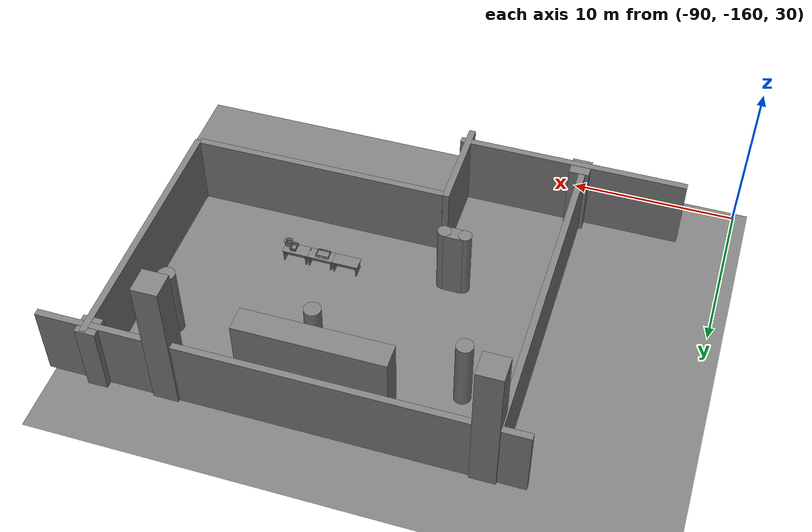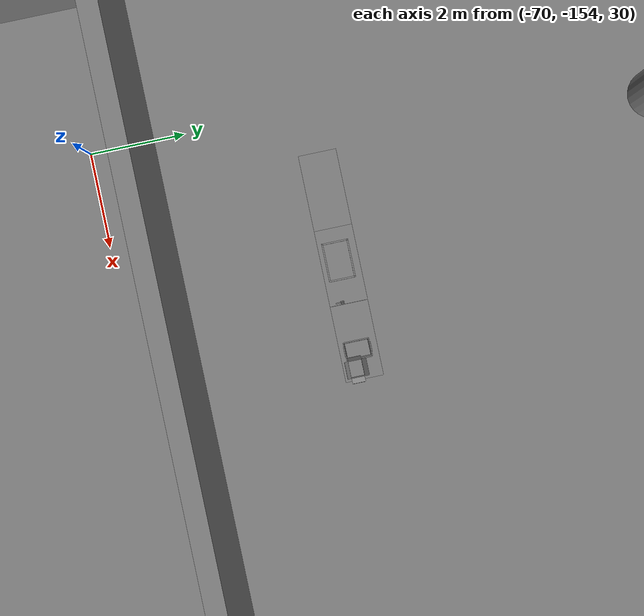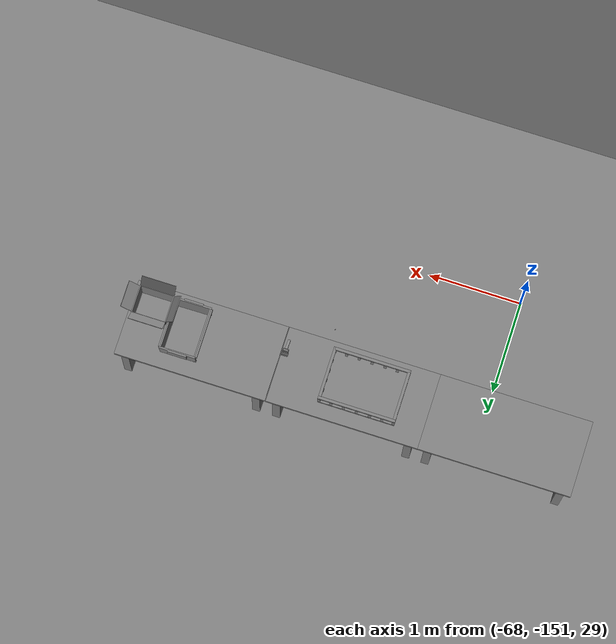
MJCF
<mujoco>
    <option gravity="0.000000000 0.000000000 -9.810000420" timestep="0.0049999999" integrator="implicitfast" density="1.225" viscosity="1.8000001e-05" noslip_iterations="10" iterations="100" sdf_iterations="50">
        <flag multiccd="disable"/>
    </option>
    <size memory="1000M"/>
    <compiler coordinate="local"/>
    <worldbody>
        <light cutoff="30" pos="0 1 1" dir="0 -1 -2"/>
        <light cutoff="30" pos="0 -1 1" dir="0 1 -2"/>
        <body pos="-64.866622925 -149.383972168 30.183746338" euler="89.999992371 89.999946594 0.000000000" name="openloong_gripper_2f85_fix_base_usda_bluebox_01">
            <geom contype="1" conaffinity="1" density="1000" type="box" material="" rgba="0.500000000 0.500000000 0.500000000 1.000000000" solimp="0.899999976 0.949999988 0.001000000" friction="1.000000000 0.005000000 0.000100000" solref="0.020000000 1.000000000" margin="0" condim="3" group="0" pos="0.276596069 0.187225342 0.000061035" quat="0.707107008 0.000077501 0.707106471 0.000077456" size="0.100000001 0.057999998 0.010000000" name="openloong_gripper_2f85_fix_base_usda_geom_458AFF90_19E1_4B68_A55E_F3559520D661"/>
            <geom contype="1" conaffinity="1" density="1000" type="box" material="" rgba="0.500000000 0.500000000 0.500000000 1.000000000" solimp="0.899999976 0.949999988 0.001000000" friction="1.000000000 0.005000000 0.000100000" solref="0.020000000 1.000000000" margin="0" condim="3" group="0" pos="0.000000000 0.002883911 0.000000000" quat="1.000000000 0.000000000 0.000000000 0.000000000" size="0.254000008 0.003000000 0.172000006" name="openloong_gripper_2f85_fix_base_usda_geom_9EDDA268_208F_43C6_A574_4B39AD65F36A"/>
            <geom contype="1" conaffinity="1" density="1000" type="box" material="" rgba="0.500000000 0.500000000 0.500000000 1.000000000" solimp="0.899999976 0.949999988 0.001000000" friction="1.000000000 0.005000000 0.000100000" solref="0.020000000 1.000000000" margin="0" condim="3" group="0" pos="0.000015259 0.124874115 0.173477173" quat="0.999796450 0.020176515 -0.000000015 0.000000030" size="0.259999990 0.119999997 0.007000000" name="openloong_gripper_2f85_fix_base_usda_geom_8E710354_3A66_4E33_B96B_E58CCD302CA7"/>
            <geom contype="1" conaffinity="1" density="1000" type="box" material="" rgba="0.500000000 0.500000000 0.500000000 1.000000000" solimp="0.899999976 0.949999988 0.001000000" friction="1.000000000 0.005000000 0.000100000" solref="0.020000000 1.000000000" margin="0" condim="3" group="0" pos="0.000015259 0.124874115 -0.173477173" quat="0.999796450 -0.020176545 -0.000000015 0.000000000" size="0.259999990 0.119999997 0.007000000" name="openloong_gripper_2f85_fix_base_usda_geom_5B27AA7A_BDCA_450D_B786_22BBADEAB772"/>
            <geom contype="1" conaffinity="1" density="1000" type="box" material="" rgba="0.500000000 0.500000000 0.500000000 1.000000000" solimp="0.899999976 0.949999988 0.001000000" friction="1.000000000 0.005000000 0.000100000" solref="0.020000000 1.000000000" margin="0" condim="3" group="0" pos="0.000015259 0.214012146 0.188980103" quat="0.999913096 0.013176724 0.000000015 0.000000000" size="0.259999990 0.029999999 0.012500000" name="openloong_gripper_2f85_fix_base_usda_geom_781040B7_E3FA_4389_BA73_60F5292FBCAE"/>
            <geom contype="1" conaffinity="1" density="1000" type="box" material="" rgba="0.500000000 0.500000000 0.500000000 1.000000000" solimp="0.899999976 0.949999988 0.001000000" friction="1.000000000 0.005000000 0.000100000" solref="0.020000000 1.000000000" margin="0" condim="3" group="0" pos="-0.258346558 0.125289917 0.001876831" quat="0.702796996 -0.020792052 0.710783184 0.020769238" size="0.189999998 0.119999997 0.009000000" name="openloong_gripper_2f85_fix_base_usda_geom_2B745E52_74BE_43E8_AF04_2A148B7C46FD"/>
            <geom contype="1" conaffinity="1" density="1000" type="box" material="" rgba="0.500000000 0.500000000 0.500000000 1.000000000" solimp="0.899999976 0.949999988 0.001000000" friction="1.000000000 0.005000000 0.000100000" solref="0.020000000 1.000000000" margin="0" condim="3" group="0" pos="0.000015259 0.214012146 -0.188980103" quat="0.999913096 -0.013176769 0.000000030 0.000000015" size="0.259999990 0.029999999 0.012500000" name="openloong_gripper_2f85_fix_base_usda_geom_13FE78BC_07E6_4D30_B0DA_51CF7E59C78D"/>
            <geom contype="1" conaffinity="1" density="1000" type="box" material="" rgba="0.500000000 0.500000000 0.500000000 1.000000000" solimp="0.899999976 0.949999988 0.001000000" friction="1.000000000 0.005000000 0.000100000" solref="0.020000000 1.000000000" margin="0" condim="3" group="0" pos="-0.276596069 0.187225342 0.000061035" quat="0.707106650 0.000077441 0.707106709 0.000077456" size="0.100000001 0.057999998 0.010000000" name="openloong_gripper_2f85_fix_base_usda_geom_BE74F2EE_9ABA_40C4_BBFC_0D61FE76B3C9"/>
            <geom contype="1" conaffinity="1" density="1000" type="box" material="" rgba="0.500000000 0.500000000 0.500000000 1.000000000" solimp="0.899999976 0.949999988 0.001000000" friction="1.000000000 0.005000000 0.000100000" solref="0.020000000 1.000000000" margin="0" condim="3" group="0" pos="0.258346558 0.125289917 0.001876831" quat="0.702851534 0.018856451 0.710823834 -0.019329429" size="0.189999998 0.119999997 0.009000000" name="openloong_gripper_2f85_fix_base_usda_geom_51634D7D_4F03_4949_A643_BDC910FDAB5E"/>
            <freejoint name="openloong_gripper_2f85_fix_base_usda_bluebox_01_joint"/>
            <site size="0.005000000 0.005000000 0.005000000" rgba="0.500000000 0.500000000 0.500000000 1.000000000" pos="0.000000000 0.000000000 0.000000000" quat="0.999961913 0.008726534 0.000000000 0.000000000" group="0" type="sphere" name="openloong_gripper_2f85_fix_base_usda_bluebox_01site"/>
        </body>
        <body pos="-64.496299744 -149.491867065 30.235729218" euler="0.000000000 0.000000000 89.999946594" name="openloong_gripper_2f85_fix_base_usda_cardboardbox_01">
            <geom contype="1" conaffinity="1" density="1000" type="box" material="" rgba="0.500000000 0.500000000 0.500000000 1.000000000" solimp="0.899999976 0.949999988 0.001000000" friction="1.000000000 0.005000000 0.000100000" solref="0.020000000 1.000000000" margin="0" condim="3" group="0" pos="-0.003166199 -0.004086494 0.005052090" quat="1.000000000 0.000000000 0.000000000 0.000000000" size="0.142499998 0.177500010 0.005000000" name="openloong_gripper_2f85_fix_base_usda_geom_C0FA43DB_443F_4C81_8768_7AF6326E6531"/>
            <geom contype="1" conaffinity="1" density="1000" type="box" material="" rgba="0.500000000 0.500000000 0.500000000 1.000000000" solimp="0.899999976 0.949999988 0.001000000" friction="1.000000000 0.005000000 0.000100000" solref="0.020000000 1.000000000" margin="0" condim="3" group="0" pos="-0.003166199 0.170316696 0.150570869" quat="1.000000000 0.000000000 0.000000000 0.000000000" size="0.142499998 0.005000000 0.149999991" name="openloong_gripper_2f85_fix_base_usda_geom_3872700A_9830_4E8A_B9DD_DBCDF3AFF67E"/>
            <geom contype="1" conaffinity="1" density="1000" type="box" material="" rgba="0.500000000 0.500000000 0.500000000 1.000000000" solimp="0.899999976 0.949999988 0.001000000" friction="1.000000000 0.005000000 0.000100000" solref="0.020000000 1.000000000" margin="0" condim="3" group="0" pos="-0.147399902 -0.005307198 0.150570869" quat="1.000000000 0.000000000 0.000000000 0.000000000" size="0.005000000 0.177500010 0.149999991" name="openloong_gripper_2f85_fix_base_usda_geom_C7DD7F3C_244D_4202_9647_E055775FFF8E"/>
            <geom contype="1" conaffinity="1" density="1000" type="box" material="" rgba="0.500000000 0.500000000 0.500000000 1.000000000" solimp="0.899999976 0.949999988 0.001000000" friction="1.000000000 0.005000000 0.000100000" solref="0.020000000 1.000000000" margin="0" condim="3" group="0" pos="0.140275955 -0.005307198 0.150570869" quat="1.000000000 0.000000000 0.000000000 0.000000000" size="0.005000000 0.177500010 0.149999991" name="openloong_gripper_2f85_fix_base_usda_geom_D7F2DC90_9EA5_4D49_B95C_6D76D917A1C6"/>
            <geom contype="1" conaffinity="1" density="1000" type="box" material="" rgba="0.500000000 0.500000000 0.500000000 1.000000000" solimp="0.899999976 0.949999988 0.001000000" friction="1.000000000 0.005000000 0.000100000" solref="0.020000000 1.000000000" margin="0" condim="3" group="0" pos="-0.003166199 -0.181550980 0.150570869" quat="1.000000000 0.000000000 0.000000000 0.000000000" size="0.142499998 0.005000000 0.149999991" name="openloong_gripper_2f85_fix_base_usda_geom_F3DC9A3B_9D49_47C5_B5B8_1B292F964769"/>
            <freejoint name="openloong_gripper_2f85_fix_base_usda_cardboardbox_01_joint"/>
            <site size="0.005000000 0.005000000 0.005000000" rgba="0.500000000 0.500000000 0.500000000 1.000000000" pos="0.000000000 0.000000000 0.000000000" quat="0.999961913 0.008726535 0.000000000 0.000000000" group="0" type="sphere" name="openloong_gripper_2f85_fix_base_usda_site_FE884632_9DA9_49AC_BB57_05592C720085"/>
            <body pos="0.139160156 -0.004048347 0.301930904" euler="-179.999954224 49.383502960 179.999954224" name="openloong_gripper_2f85_fix_base_usda_A1_006">
                <geom contype="1" conaffinity="1" density="1000" type="box" material="" rgba="0.500000000 0.500000000 0.500000000 1.000000000" solimp="0.899999976 0.949999988 0.001000000" friction="1.000000000 0.005000000 0.000100000" solref="0.020000000 1.000000000" margin="0" condim="3" group="0" pos="-0.071587563 0.000009537 0.001745224" quat="0.999999881 0.000000000 0.000000000 0.000000000" size="0.071249999 0.179999992 0.002500000" name="openloong_gripper_2f85_fix_base_usda_geom_A23C70F7_0963_4FB8_B2A0_019C4149A8FB"/>
                <joint armature="0" stiffness="0.07" damping="0.0099999998" axis="0.000000 1.000000 0.000000" type="hinge" name="openloong_gripper_2f85_fix_base_usda_A1_006"/>
            </body>
            <body pos="-0.145902634 -0.004086494 0.301938057" euler="-180.000000000 -60.000011444 -180.000000000" name="openloong_gripper_2f85_fix_base_usda_A2_006">
                <geom contype="1" conaffinity="1" density="1000" type="box" material="" rgba="0.500000000 0.500000000 0.500000000 1.000000000" solimp="0.899999976 0.949999988 0.001000000" friction="1.000000000 0.005000000 0.000100000" solref="0.020000000 1.000000000" margin="0" condim="3" group="0" pos="0.071268082 0.000009537 0.002717972" quat="0.000002921 0.000000000 -0.000000030 0.999999881" size="0.071249999 0.179999992 0.002500000" name="openloong_gripper_2f85_fix_base_usda_geom_C9392AB3_A356_4103_9E2B_7C1B4199FDA3"/>
                <joint armature="0" stiffness="0.07" damping="0.0099999998" axis="0.000000 1.000000 0.000000" type="hinge" name="openloong_gripper_2f85_fix_base_usda_A2_006"/>
            </body>
            <body pos="-0.003385544 0.175991058 0.301930904" euler="-125.858116150 -0.000004561 0.000002331" name="openloong_gripper_2f85_fix_base_usda_B2_006">
                <geom contype="1" conaffinity="1" density="1000" type="box" material="" rgba="0.500000000 0.500000000 0.500000000 1.000000000" solimp="0.899999976 0.949999988 0.001000000" friction="1.000000000 0.005000000 0.000100000" solref="0.020000000 1.000000000" margin="0" condim="3" group="0" pos="0.000009537 -0.070939064 -0.002470016" quat="0.999614120 0.027776197 -0.000000015 0.000000030" size="0.137500003 0.064999998 0.005000000" name="openloong_gripper_2f85_fix_base_usda_geom_05ACCD66_E95E_47BF_B29C_9A32AC36F495"/>
                <joint armature="0" stiffness="0.07" damping="0.0099999998" axis="1.000000 0.000000 0.000000" type="hinge" name="openloong_gripper_2f85_fix_base_usda_B2_006"/>
            </body>
            <body pos="-0.003385544 -0.184140205 0.301938057" euler="147.805557251 0.000000000 0.000000000" name="openloong_gripper_2f85_fix_base_usda_B1_006">
                <geom contype="1" conaffinity="1" density="1000" type="box" material="" rgba="0.500000000 0.500000000 0.500000000 1.000000000" solimp="0.899999976 0.949999988 0.001000000" friction="1.000000000 0.005000000 0.000100000" solref="0.020000000 1.000000000" margin="0" condim="3" group="0" pos="-0.000028610 0.070202351 -0.002703667" quat="0.999614179 -0.027776167 0.000000000 0.000000000" size="0.137500003 0.064999998 0.005000000" name="openloong_gripper_2f85_fix_base_usda_geom_0B422746_63F4_4E65_A55D_0FF06D68CABB"/>
                <joint armature="0" stiffness="0.07" damping="0.0099999998" axis="1.000000 0.000000 0.000000" type="hinge" name="openloong_gripper_2f85_fix_base_usda_B1_006"/>
            </body>
        </body>
        <body pos="-65.882858276 -149.481979370 30.229999542" euler="-64.487716675 0.000000000 0.000000000" name="openloong_gripper_2f85_fix_base_usda_Barcode">
            <geom contype="1" conaffinity="1" density="1000" type="box" material="" rgba="0.500000000 0.500000000 0.500000000 1.000000000" solimp="0.899999976 0.949999988 0.001000000" friction="1.000000000 0.005000000 0.000100000" solref="0.020000000 1.000000000" margin="0" condim="3" group="0" pos="0.000000000 0.013038635 0.001419067" quat="0.000000000 0.000000000 0.000000000 1.000000119" size="0.034000002 0.010000000 0.017999999" name="openloong_gripper_2f85_fix_base_usda_geom_37ACE878_9E2A_4714_9867_D4194AC20DA9"/>
            <geom contype="1" conaffinity="1" density="1000" type="box" material="" rgba="0.500000000 0.500000000 0.500000000 1.000000000" solimp="0.899999976 0.949999988 0.001000000" friction="1.000000000 0.005000000 0.000100000" solref="0.020000000 1.000000000" margin="0" condim="3" group="0" pos="0.000000000 -0.035301208 -0.007095337" quat="0.000000000 0.000000000 -0.043619365 0.999048233" size="0.028999999 0.010000000 0.020000000" name="openloong_gripper_2f85_fix_base_usda_geom_69283807_4A23_4B2A_8912_F16C95E2B00D"/>
            <geom contype="1" conaffinity="1" density="1000" type="box" material="" rgba="0.500000000 0.500000000 0.500000000 1.000000000" solimp="0.899999976 0.949999988 0.001000000" friction="1.000000000 0.005000000 0.000100000" solref="0.020000000 1.000000000" margin="0" condim="3" group="0" pos="0.000000000 -0.043411255 -0.011749268" quat="0.922262907 0.386563420 0.000000000 0.000000000" size="0.026000001 0.010000000 0.020000000" name="openloong_gripper_2f85_fix_base_usda_geom_43C5E8C9_866D_4A9C_AF61_288A5934909D"/>
            <geom contype="1" conaffinity="1" density="1000" type="box" material="" rgba="0.500000000 0.500000000 0.500000000 1.000000000" solimp="0.899999976 0.949999988 0.001000000" friction="1.000000000 0.005000000 0.000100000" solref="0.020000000 1.000000000" margin="0" condim="3" group="0" pos="0.000000000 -0.016967773 -0.031860352" quat="0.000000000 0.000000000 0.000000000 1.000000119" size="0.008000000 0.010000000 0.013000000" name="openloong_gripper_2f85_fix_base_usda_geom_84B1A2D8_41DD_4CAD_9210_432629EA0612"/>
            <geom contype="1" conaffinity="1" density="1000" type="box" material="" rgba="0.500000000 0.500000000 0.500000000 1.000000000" solimp="0.899999976 0.949999988 0.001000000" friction="1.000000000 0.005000000 0.000100000" solref="0.020000000 1.000000000" margin="0" condim="3" group="0" pos="0.000000000 -0.001869202 0.000312805" quat="0.953716993 0.300705761 0.000000000 0.000000000" size="0.032000002 0.010000000 0.018999999" name="openloong_gripper_2f85_fix_base_usda_geom_AF5474F4_9A26_4635_8A7A_57439F31648D"/>
            <geom contype="1" conaffinity="1" density="1000" type="box" material="" rgba="0.500000000 0.500000000 0.500000000 1.000000000" solimp="0.899999976 0.949999988 0.001000000" friction="1.000000000 0.005000000 0.000100000" solref="0.020000000 1.000000000" margin="0" condim="3" group="0" pos="0.000000000 -0.019531250 -0.003173828" quat="0.953716993 0.300705761 0.000000000 0.000000000" size="0.030999999 0.010000000 0.020000000" name="openloong_gripper_2f85_fix_base_usda_geom_2A078AAF_D0B2_4CE5_87D5_556FD7DC9ADD"/>
            <geom contype="1" conaffinity="1" density="1000" type="box" material="" rgba="0.500000000 0.500000000 0.500000000 1.000000000" solimp="0.899999976 0.949999988 0.001000000" friction="1.000000000 0.005000000 0.000100000" solref="0.020000000 1.000000000" margin="0" condim="3" group="0" pos="0.000000000 -0.035301208 -0.007095337" quat="0.953716993 0.300705761 0.000000000 0.000000000" size="0.028999999 0.010000000 0.020000000" name="openloong_gripper_2f85_fix_base_usda_geom_2D902871_BCC9_4C66_B776_D42725AFF1F9"/>
            <geom contype="1" conaffinity="1" density="1000" type="box" material="" rgba="0.500000000 0.500000000 0.500000000 1.000000000" solimp="0.899999976 0.949999988 0.001000000" friction="1.000000000 0.005000000 0.000100000" solref="0.020000000 1.000000000" margin="0" condim="3" group="0" pos="0.000000000 -0.042617798 -0.071121216" quat="0.000000000 0.000000000 0.000000000 1.000000119" size="0.013000000 0.021000000 0.059999999" name="openloong_gripper_2f85_fix_base_usda_geom_EB8EADD9_B10D_4F8A_86B1_221C641C7B86"/>
            <freejoint name="openloong_gripper_2f85_fix_base_usda_Barcode_joint"/>
            <site size="0.005000000 0.005000000 0.005000000" rgba="0.500000000 0.500000000 0.500000000 1.000000000" pos="0.000000000 0.000000000 0.000000000" quat="1.000000000 0.000000000 0.000000000 0.000000000" group="0" type="sphere" name="openloong_gripper_2f85_fix_base_usda_Barcode_site"/>
        </body>
        <body pos="-66.745018005 -149.392349243 30.184000015" euler="0.000000000 0.000000000 89.999946594" name="[22331100664914]_Basket_01">
            <geom contype="1" conaffinity="1" density="1000" type="box" material="" rgba="0.500000000 0.500000000 0.500000000 1.000000000" solimp="0.899999976 0.949999988 0.001000000" friction="1.000000000 0.005000000 0.000100000" solref="0.020000000 1.000000000" margin="0" condim="3" group="0" pos="-0.052425385 0.389207840 0.089787483" quat="0.707107008 0.000000000 0.000000000 0.707106411" size="0.014249999 0.014249999 0.059999999" name="[22331100664914]_geom_25932A96_E08C_4074_BEF6_5BBDD8BB22B7"/>
            <geom contype="1" conaffinity="1" density="1000" type="box" material="" rgba="0.500000000 0.500000000 0.500000000 1.000000000" solimp="0.899999976 0.949999988 0.001000000" friction="1.000000000 0.005000000 0.000100000" solref="0.020000000 1.000000000" margin="0" condim="3" group="0" pos="0.264015198 -0.133043289 0.089787483" quat="0.707107008 0.000000000 0.000000000 0.707106411" size="0.014249999 0.014249999 0.059999999" name="[22331100664914]_geom_DECDD94F_0129_4A23_AECC_134F0DB72E46"/>
            <geom contype="1" conaffinity="1" density="1000" type="box" material="" rgba="0.500000000 0.500000000 0.500000000 1.000000000" solimp="0.899999976 0.949999988 0.001000000" friction="1.000000000 0.005000000 0.000100000" solref="0.020000000 1.000000000" margin="0" condim="3" group="0" pos="-0.264015198 -0.265548706 0.089793205" quat="0.707107008 0.000000000 0.000000000 0.707106411" size="0.014249999 0.014249999 0.059999999" name="[22331100664914]_geom_E583D9B8_C2BC_4C54_BD6E_F7E0B8EF5EBB"/>
            <geom contype="1" conaffinity="1" density="1000" type="box" material="" rgba="0.500000000 0.500000000 0.500000000 1.000000000" solimp="0.899999976 0.949999988 0.001000000" friction="1.000000000 0.005000000 0.000100000" solref="0.020000000 1.000000000" margin="0" condim="3" group="0" pos="-0.160263062 -0.389322281 0.089793205" quat="0.707107008 0.000000000 0.000000000 0.707106411" size="0.014249999 0.014249999 0.059999999" name="[22331100664914]_geom_6B080800_86F4_4D8C_B4E6_7AE5E357ADF6"/>
            <geom contype="1" conaffinity="1" density="1000" type="box" material="" rgba="0.500000000 0.500000000 0.500000000 1.000000000" solimp="0.899999976 0.949999988 0.001000000" friction="1.000000000 0.005000000 0.000100000" solref="0.020000000 1.000000000" margin="0" condim="3" group="0" pos="0.162265778 -0.389322281 0.089787483" quat="0.707107008 0.000000000 0.000000000 0.707106411" size="0.014249999 0.014249999 0.059999999" name="[22331100664914]_geom_DA4AE131_8BF5_483E_A1EE_1447C8255777"/>
            <geom contype="1" conaffinity="1" density="1000" type="box" material="" rgba="0.500000000 0.500000000 0.500000000 1.000000000" solimp="0.899999976 0.949999988 0.001000000" friction="1.000000000 0.005000000 0.000100000" solref="0.020000000 1.000000000" margin="0" condim="3" group="0" pos="0.264015198 0.389207840 0.089787483" quat="0.707107008 0.000000000 0.000000000 0.707106411" size="0.014249999 0.014249999 0.059999999" name="[22331100664914]_geom_00A8668B_32AE_417E_9B45_2C15084D6164"/>
            <geom contype="1" conaffinity="1" density="1000" type="box" material="" rgba="0.500000000 0.500000000 0.500000000 1.000000000" solimp="0.899999976 0.949999988 0.001000000" friction="1.000000000 0.005000000 0.000100000" solref="0.020000000 1.000000000" margin="0" condim="3" group="0" pos="-0.264015198 -0.133043289 0.089793205" quat="0.707107008 0.000000000 0.000000000 0.707106411" size="0.014249999 0.014249999 0.059999999" name="[22331100664914]_geom_67B1A915_BFEF_4C67_9413_536E72E4D634"/>
            <geom contype="1" conaffinity="1" density="1000" type="box" material="" rgba="0.500000000 0.500000000 0.500000000 1.000000000" solimp="0.899999976 0.949999988 0.001000000" friction="1.000000000 0.005000000 0.000100000" solref="0.020000000 1.000000000" margin="0" condim="3" group="0" pos="-0.264026642 0.269256592 0.089793205" quat="0.707107008 0.000000000 0.000000000 0.707106411" size="0.014249999 0.014249999 0.059999999" name="[22331100664914]_geom_AD5710F3_F3C3_40EB_9001_175B8FDE27B1"/>
            <geom contype="1" conaffinity="1" density="1000" type="box" material="" rgba="0.500000000 0.500000000 0.500000000 1.000000000" solimp="0.899999976 0.949999988 0.001000000" friction="1.000000000 0.005000000 0.000100000" solref="0.020000000 1.000000000" margin="0" condim="3" group="0" pos="0.054462433 0.389207840 0.089787483" quat="0.707107008 0.000000000 0.000000000 0.707106411" size="0.014249999 0.014249999 0.059999999" name="[22331100664914]_geom_3B28EC47_1398_4068_B4B0_DCB751962437"/>
            <geom contype="1" conaffinity="1" density="1000" type="box" material="" rgba="0.500000000 0.500000000 0.500000000 1.000000000" solimp="0.899999976 0.949999988 0.001000000" friction="1.000000000 0.005000000 0.000100000" solref="0.020000000 1.000000000" margin="0" condim="3" group="0" pos="0.054462433 -0.389322281 0.089787483" quat="0.707107008 0.000000000 0.000000000 0.707106411" size="0.014249999 0.014249999 0.059999999" name="[22331100664914]_geom_9A4E3C47_2D10_4ABF_837A_80391B60C678"/>
            <geom contype="1" conaffinity="1" density="1000" type="box" material="" rgba="0.500000000 0.500000000 0.500000000 1.000000000" solimp="0.899999976 0.949999988 0.001000000" friction="1.000000000 0.005000000 0.000100000" solref="0.020000000 1.000000000" margin="0" condim="3" group="0" pos="0.264015198 0.269256592 0.089793205" quat="0.707107008 0.000000000 0.000000000 0.707106411" size="0.014249999 0.014249999 0.059999999" name="[22331100664914]_geom_1F734EB7_D662_4005_A22F_23B69008D001"/>
            <geom contype="1" conaffinity="1" density="1000" type="box" material="" rgba="0.500000000 0.500000000 0.500000000 1.000000000" solimp="0.899999976 0.949999988 0.001000000" friction="1.000000000 0.005000000 0.000100000" solref="0.020000000 1.000000000" margin="0" condim="3" group="0" pos="0.264015198 -0.389322281 0.089787483" quat="0.707107008 0.000000000 0.000000000 0.707106411" size="0.014249999 0.014249999 0.059999999" name="[22331100664914]_geom_58BD7BCF_B798_463B_B1E5_5DC439DDFEFF"/>
            <geom contype="1" conaffinity="1" density="1000" type="box" material="" rgba="0.500000000 0.500000000 0.500000000 1.000000000" solimp="0.899999976 0.949999988 0.001000000" friction="1.000000000 0.005000000 0.000100000" solref="0.020000000 1.000000000" margin="0" condim="3" group="0" pos="0.000000000 0.000000000 0.015998840" quat="0.707107008 0.000000000 0.000000000 0.707106411" size="0.403499991 0.279000014 0.015750000" name="[22331100664914]_geom_AC72219A_5388_474A_AAE9_2FC949A2EB4E"/>
            <geom contype="1" conaffinity="1" density="1000" type="box" material="" rgba="0.500000000 0.500000000 0.500000000 1.000000000" solimp="0.899999976 0.949999988 0.001000000" friction="1.000000000 0.005000000 0.000100000" solref="0.020000000 1.000000000" margin="0" condim="3" group="0" pos="0.000000000 -0.389476776 0.163619041" quat="0.707107008 0.000000000 0.000000000 0.707106411" size="0.015000000 0.277500004 0.015750000" name="[22331100664914]_geom_360D71A9_EFB3_42D2_9DDA_1D3177360651"/>
            <geom contype="1" conaffinity="1" density="1000" type="box" material="" rgba="0.500000000 0.500000000 0.500000000 1.000000000" solimp="0.899999976 0.949999988 0.001000000" friction="1.000000000 0.005000000 0.000100000" solref="0.020000000 1.000000000" margin="0" condim="3" group="0" pos="0.162265778 0.389207840 0.089787483" quat="0.707107008 0.000000000 0.000000000 0.707106411" size="0.014249999 0.014249999 0.059999999" name="[22331100664914]_geom_7F2365A0_0901_449D_B85B_FA7E759E4326"/>
            <geom contype="1" conaffinity="1" density="1000" type="box" material="" rgba="0.500000000 0.500000000 0.500000000 1.000000000" solimp="0.899999976 0.949999988 0.001000000" friction="1.000000000 0.005000000 0.000100000" solref="0.020000000 1.000000000" margin="0" condim="3" group="0" pos="0.000000000 0.389471054 0.163619041" quat="0.707107008 0.000000000 0.000000000 0.707106411" size="0.015000000 0.277500004 0.015750000" name="[22331100664914]_geom_A32F919F_1B69_413C_AD53_90D1D746D389"/>
            <geom contype="1" conaffinity="1" density="1000" type="box" material="" rgba="0.500000000 0.500000000 0.500000000 1.000000000" solimp="0.899999976 0.949999988 0.001000000" friction="1.000000000 0.005000000 0.000100000" solref="0.020000000 1.000000000" margin="0" condim="3" group="0" pos="-0.263511658 0.000000000 0.163619041" quat="0.707107008 0.000000000 0.000000000 0.707106411" size="0.403499991 0.015000000 0.015750000" name="[22331100664914]_geom_86F43B8E_9FFB_4381_B636_967738C6E598"/>
            <geom contype="1" conaffinity="1" density="1000" type="box" material="" rgba="0.500000000 0.500000000 0.500000000 1.000000000" solimp="0.899999976 0.949999988 0.001000000" friction="1.000000000 0.005000000 0.000100000" solref="0.020000000 1.000000000" margin="0" condim="3" group="0" pos="-0.264015198 0.141334534 0.089793205" quat="0.707107008 0.000000000 0.000000000 0.707106411" size="0.014249999 0.014249999 0.059999999" name="[22331100664914]_geom_9DE3CBA0_C979_46BD_8188_B99ACF7E4E47"/>
            <geom contype="1" conaffinity="1" density="1000" type="box" material="" rgba="0.500000000 0.500000000 0.500000000 1.000000000" solimp="0.899999976 0.949999988 0.001000000" friction="1.000000000 0.005000000 0.000100000" solref="0.020000000 1.000000000" margin="0" condim="3" group="0" pos="0.264015198 -0.265548706 0.089787483" quat="0.707107008 0.000000000 0.000000000 0.707106411" size="0.014249999 0.014249999 0.059999999" name="[22331100664914]_geom_B58B9499_1C8F_4B7F_8420_1DB5F3597D94"/>
            <geom contype="1" conaffinity="1" density="1000" type="box" material="" rgba="0.500000000 0.500000000 0.500000000 1.000000000" solimp="0.899999976 0.949999988 0.001000000" friction="1.000000000 0.005000000 0.000100000" solref="0.020000000 1.000000000" margin="0" condim="3" group="0" pos="-0.160263062 0.389207840 0.089787483" quat="0.707107008 0.000000000 0.000000000 0.707106411" size="0.014249999 0.014249999 0.059999999" name="[22331100664914]_geom_3C64DE3F_D29E_4ABF_9EF4_DBC58261A04E"/>
            <geom contype="1" conaffinity="1" density="1000" type="box" material="" rgba="0.500000000 0.500000000 0.500000000 1.000000000" solimp="0.899999976 0.949999988 0.001000000" friction="1.000000000 0.005000000 0.000100000" solref="0.020000000 1.000000000" margin="0" condim="3" group="0" pos="-0.052425385 -0.389322281 0.089787483" quat="0.707107008 0.000000000 0.000000000 0.707106411" size="0.014249999 0.014249999 0.059999999" name="[22331100664914]_geom_2FD3C886_0B33_4A43_B24F_AC1DA7117550"/>
            <geom contype="1" conaffinity="1" density="1000" type="box" material="" rgba="0.500000000 0.500000000 0.500000000 1.000000000" solimp="0.899999976 0.949999988 0.001000000" friction="1.000000000 0.005000000 0.000100000" solref="0.020000000 1.000000000" margin="0" condim="3" group="0" pos="-0.264026642 -0.389322281 0.089793205" quat="0.707107008 0.000000000 0.000000000 0.707106411" size="0.014249999 0.014249999 0.059999999" name="[22331100664914]_geom_97A308FB_073A_42C8_85E5_28E56578BD21"/>
            <geom contype="1" conaffinity="1" density="1000" type="box" material="" rgba="0.500000000 0.500000000 0.500000000 1.000000000" solimp="0.899999976 0.949999988 0.001000000" friction="1.000000000 0.005000000 0.000100000" solref="0.020000000 1.000000000" margin="0" condim="3" group="0" pos="0.264015198 0.141334534 0.089787483" quat="0.707107008 0.000000000 0.000000000 0.707106411" size="0.014249999 0.014249999 0.059999999" name="[22331100664914]_geom_5B26AB77_730D_47B1_86AF_5DE8CF75B3C9"/>
            <geom contype="1" conaffinity="1" density="1000" type="box" material="" rgba="0.500000000 0.500000000 0.500000000 1.000000000" solimp="0.899999976 0.949999988 0.001000000" friction="1.000000000 0.005000000 0.000100000" solref="0.020000000 1.000000000" margin="0" condim="3" group="0" pos="-0.264015198 0.389207840 0.089793205" quat="0.707107008 0.000000000 0.000000000 0.707106411" size="0.014249999 0.014249999 0.059999999" name="[22331100664914]_geom_46722822_BD3E_473C_AD0C_0162E7BCBF1D"/>
            <geom contype="1" conaffinity="1" density="1000" type="box" material="" rgba="0.500000000 0.500000000 0.500000000 1.000000000" solimp="0.899999976 0.949999988 0.001000000" friction="1.000000000 0.005000000 0.000100000" solref="0.020000000 1.000000000" margin="0" condim="3" group="0" pos="0.264015198 0.004480362 0.089787483" quat="0.707107008 0.000000000 0.000000000 0.707106411" size="0.014249999 0.014249999 0.059999999" name="[22331100664914]_geom_24053CAF_F052_4EC1_AF61_6369A2F62BF5"/>
            <geom contype="1" conaffinity="1" density="1000" type="box" material="" rgba="0.500000000 0.500000000 0.500000000 1.000000000" solimp="0.899999976 0.949999988 0.001000000" friction="1.000000000 0.005000000 0.000100000" solref="0.020000000 1.000000000" margin="0" condim="3" group="0" pos="0.263694763 -0.000011444 0.163619041" quat="0.707107008 0.000000000 0.000000000 0.707106411" size="0.403499991 0.015000000 0.015750000" name="[22331100664914]_geom_25DF68CB_805B_4E57_B103_5E18A8E14C16"/>
            <geom contype="1" conaffinity="1" density="1000" type="box" material="" rgba="0.500000000 0.500000000 0.500000000 1.000000000" solimp="0.899999976 0.949999988 0.001000000" friction="1.000000000 0.005000000 0.000100000" solref="0.020000000 1.000000000" margin="0" condim="3" group="0" pos="-0.264015198 0.004480362 0.089793205" quat="0.707107008 0.000000000 0.000000000 0.707106411" size="0.014249999 0.014249999 0.059999999" name="[22331100664914]_geom_0D84C5BB_AE82_45A1_80DA_8DFADA9B6DC2"/>
            <freejoint name="[22331100664914]_joint_BD33C925_0EAD_4BEB_8BB5_E53A496C2630"/>
        </body>
        <body pos="0.000000000 0.000000000 0.000000000" euler="0.000000000 0.000000000 0.000000000" name="Static Objects_Static Objects">
            <geom contype="1" conaffinity="1" density="1000" type="box" material="" rgba="0.500000000 0.500000000 0.500000000 1.000000000" solimp="0.899999976 0.949999988 0.001000000" friction="1.000000000 0.005000000 0.000100000" solref="0.020000000 1.000000000" margin="0" condim="3" group="0" pos="-67.544113159 -149.365814209 29.727830887" quat="0.500000417 0.499999970 0.499999553 0.499999970" size="0.381000012 0.319999993 0.041000001" name="Static Objects_geom_CC3499D8_AE60_4052_BCDC_01BF5BE2C298"/>
            <geom contype="1" conaffinity="1" density="1000" type="box" material="" rgba="0.500000000 0.500000000 0.500000000 1.000000000" solimp="0.899999976 0.949999988 0.001000000" friction="1.000000000 0.005000000 0.000100000" solref="0.020000000 1.000000000" margin="0" condim="3" group="0" pos="-68.239501953 -149.365814209 30.086868286" quat="0.500000417 0.499999970 0.499999553 0.499999970" size="0.370999992 0.039500002 0.745000005" name="Static Objects_geom_21772E41_73B0_41F2_BBE1_7D82875ACC5C"/>
            <geom contype="1" conaffinity="1" density="1000" type="box" material="" rgba="0.500000000 0.500000000 0.500000000 1.000000000" solimp="0.899999976 0.949999988 0.001000000" friction="1.000000000 0.005000000 0.000100000" solref="0.020000000 1.000000000" margin="0" condim="3" group="0" pos="-68.239501953 -149.365814209 30.147235870" quat="0.500000417 0.499999970 0.499999553 0.499999970" size="0.400000006 0.022000000 0.800000012" name="Static Objects_geom_DD27A232_8568_4086_A824_7D8F518434A9"/>
            <geom contype="1" conaffinity="1" density="1000" type="box" material="" rgba="0.500000000 0.500000000 0.500000000 1.000000000" solimp="0.899999976 0.949999988 0.001000000" friction="1.000000000 0.005000000 0.000100000" solref="0.020000000 1.000000000" margin="0" condim="3" group="0" pos="-68.934890747 -149.365814209 29.727830887" quat="0.500000417 0.499999970 0.499999553 0.499999970" size="0.381000012 0.319999993 0.041000001" name="Static Objects_geom_C038DC57_B302_44B2_BE41_A60C5BC934F6"/>
            <geom contype="1" conaffinity="1" density="1000" type="box" material="" rgba="0.500000000 0.500000000 0.500000000 1.000000000" solimp="0.899999976 0.949999988 0.001000000" friction="1.000000000 0.005000000 0.000100000" solref="0.020000000 1.000000000" margin="0" condim="3" group="0" pos="-68.239501953 -149.365814209 29.561563492" quat="0.500000417 0.499999970 0.499999553 0.499999970" size="0.020000000 0.022000000 0.660000026" name="Static Objects_geom_B2EDF8E3_6610_48A7_84E2_2EBD22FE9B77"/>
            <geom contype="1" conaffinity="1" density="1000" type="box" material="" rgba="0.500000000 0.500000000 0.500000000 1.000000000" solimp="0.899999976 0.949999988 0.001000000" friction="1.000000000 0.005000000 0.000100000" solref="0.020000000 1.000000000" margin="0" condim="3" group="0" pos="-65.945671082 -149.365814209 29.727830887" quat="0.500000417 0.499999970 0.499999553 0.499999970" size="0.381000012 0.319999993 0.041000001" name="Static Objects_geom_FE67CC59_E85F_40CC_8F3F_6DCD9858B18A"/>
            <geom contype="1" conaffinity="1" density="1000" type="box" material="" rgba="0.500000000 0.500000000 0.500000000 1.000000000" solimp="0.899999976 0.949999988 0.001000000" friction="1.000000000 0.005000000 0.000100000" solref="0.020000000 1.000000000" margin="0" condim="3" group="0" pos="-66.641059875 -149.365814209 30.086868286" quat="0.500000417 0.499999970 0.499999553 0.499999970" size="0.370999992 0.039500002 0.745000005" name="Static Objects_geom_9F5EEA8B_2139_4A78_A56B_F02231308B7C"/>
            <geom contype="1" conaffinity="1" density="1000" type="box" material="" rgba="0.500000000 0.500000000 0.500000000 1.000000000" solimp="0.899999976 0.949999988 0.001000000" friction="1.000000000 0.005000000 0.000100000" solref="0.020000000 1.000000000" margin="0" condim="3" group="0" pos="-66.641059875 -149.365814209 30.147235870" quat="0.500000417 0.499999970 0.499999553 0.499999970" size="0.400000006 0.022000000 0.800000012" name="Static Objects_geom_8CE589C5_4D49_4C57_9AD4_8577C1869F10"/>
            <geom contype="1" conaffinity="1" density="1000" type="box" material="" rgba="0.500000000 0.500000000 0.500000000 1.000000000" solimp="0.899999976 0.949999988 0.001000000" friction="1.000000000 0.005000000 0.000100000" solref="0.020000000 1.000000000" margin="0" condim="3" group="0" pos="-67.336448669 -149.365814209 29.727830887" quat="0.500000417 0.499999970 0.499999553 0.499999970" size="0.381000012 0.319999993 0.041000001" name="Static Objects_geom_F99F3438_5EA1_421D_81C3_9951B2CA4955"/>
            <geom contype="1" conaffinity="1" density="1000" type="box" material="" rgba="0.500000000 0.500000000 0.500000000 1.000000000" solimp="0.899999976 0.949999988 0.001000000" friction="1.000000000 0.005000000 0.000100000" solref="0.020000000 1.000000000" margin="0" condim="3" group="0" pos="-66.641059875 -149.365814209 29.561563492" quat="0.500000417 0.499999970 0.499999553 0.499999970" size="0.020000000 0.022000000 0.660000026" name="Static Objects_geom_AAA6D907_3425_4670_B8A0_C60DA60F8422"/>
            <geom contype="1" conaffinity="1" density="1000" type="box" material="" rgba="0.500000000 0.500000000 0.500000000 1.000000000" solimp="0.899999976 0.949999988 0.001000000" friction="1.000000000 0.005000000 0.000100000" solref="0.020000000 1.000000000" margin="0" condim="3" group="0" pos="-64.338577271 -149.365814209 29.727830887" quat="0.500000417 0.499999970 0.499999553 0.499999970" size="0.381000012 0.319999993 0.041000001" name="Static Objects_geom_DBE7B736_1A45_487B_8182_E4E3EB2BCA46"/>
            <geom contype="1" conaffinity="1" density="1000" type="box" material="" rgba="0.500000000 0.500000000 0.500000000 1.000000000" solimp="0.899999976 0.949999988 0.001000000" friction="1.000000000 0.005000000 0.000100000" solref="0.020000000 1.000000000" margin="0" condim="3" group="0" pos="-65.033966064 -149.365814209 30.086868286" quat="0.500000417 0.499999970 0.499999553 0.499999970" size="0.370999992 0.039500002 0.745000005" name="Static Objects_geom_F3F89BE3_4E56_41EC_A900_6FDAFCC9FA61"/>
            <geom contype="1" conaffinity="1" density="1000" type="box" material="" rgba="0.500000000 0.500000000 0.500000000 1.000000000" solimp="0.899999976 0.949999988 0.001000000" friction="1.000000000 0.005000000 0.000100000" solref="0.020000000 1.000000000" margin="0" condim="3" group="0" pos="-65.033966064 -149.365814209 30.147235870" quat="0.500000417 0.499999970 0.499999553 0.499999970" size="0.400000006 0.022000000 0.800000012" name="Static Objects_geom_49F220B3_FD96_4502_B288_C70B44FBC149"/>
            <geom contype="1" conaffinity="1" density="1000" type="box" material="" rgba="0.500000000 0.500000000 0.500000000 1.000000000" solimp="0.899999976 0.949999988 0.001000000" friction="1.000000000 0.005000000 0.000100000" solref="0.020000000 1.000000000" margin="0" condim="3" group="0" pos="-65.729354858 -149.365814209 29.727830887" quat="0.500000417 0.499999970 0.499999553 0.499999970" size="0.381000012 0.319999993 0.041000001" name="Static Objects_geom_4ED31EF6_57B1_4B83_8298_FCBA9ACD9789"/>
            <geom contype="1" conaffinity="1" density="1000" type="box" material="" rgba="0.500000000 0.500000000 0.500000000 1.000000000" solimp="0.899999976 0.949999988 0.001000000" friction="1.000000000 0.005000000 0.000100000" solref="0.020000000 1.000000000" margin="0" condim="3" group="0" pos="-65.033966064 -149.365814209 29.561563492" quat="0.500000417 0.499999970 0.499999553 0.499999970" size="0.020000000 0.022000000 0.660000026" name="Static Objects_geom_7713FD7E_BC63_45F9_AB9D_C3E65B171A32"/>
            <geom contype="1" conaffinity="1" density="1000" type="box" material="" rgba="0.500000000 0.500000000 0.500000000 1.000000000" solimp="0.899999976 0.949999988 0.001000000" friction="1.000000000 0.005000000 0.000100000" solref="0.020000000 1.000000000" margin="0" condim="3" group="0" pos="-61.754566193 -137.853729248 33.906845093" quat="0.707107067 0.000000000 0.000000000 0.707106471" size="0.759999990 0.759999990 4.500000000" name="Static Objects_geom_029CA21A_D351_408D_B6EC_1D437EE9ABC0"/>
            <geom contype="1" conaffinity="1" density="1000" type="box" material="" rgba="0.500000000 0.500000000 0.500000000 1.000000000" solimp="0.899999976 0.949999988 0.001000000" friction="1.000000000 0.005000000 0.000100000" solref="0.020000000 1.000000000" margin="0" condim="3" group="0" pos="-57.511135101 -144.927108765 31.707921982" quat="1.000000000 0.000000000 0.000000000 0.000000000" size="0.200000003 8.000000000 2.299999952" name="Static Objects_geom_63047EE0_CE22_46C6_90AF_748D9A8104AA"/>
            <geom contype="1" conaffinity="1" density="1000" type="box" material="" rgba="0.500000000 0.500000000 0.500000000 1.000000000" solimp="0.899999976 0.949999988 0.001000000" friction="1.000000000 0.005000000 0.000100000" solref="0.020000000 1.000000000" margin="0" condim="3" group="0" pos="-80.517646790 -157.574050903 31.688196182" quat="0.707107067 0.000000000 0.000000000 0.707106471" size="0.600000024 0.600000024 2.299999952" name="Static Objects_geom_4E6B27E5_CD1D_4579_8484_4F9F3246ED56"/>
            <geom contype="1" conaffinity="1" density="1000" type="box" material="" rgba="0.500000000 0.500000000 0.500000000 1.000000000" solimp="0.899999976 0.949999988 0.001000000" friction="1.000000000 0.005000000 0.000100000" solref="0.020000000 1.000000000" margin="0" condim="3" group="0" pos="-80.711044312 -147.414932251 31.666158676" quat="1.000000000 0.000000000 0.000000000 0.000000000" size="0.200000003 10.000000000 2.299999952" name="Static Objects_geom_FC7E59B6_6F91_4718_A0C9_C6C80E3E3E37"/>
            <geom contype="1" conaffinity="1" density="1000" type="box" material="" rgba="0.500000000 0.500000000 0.500000000 1.000000000" solimp="0.899999976 0.949999988 0.001000000" friction="1.000000000 0.005000000 0.000100000" solref="0.020000000 1.000000000" margin="0" condim="3" group="0" pos="-57.687217712 -137.434692383 31.688196182" quat="0.707107067 0.000000000 0.000000000 0.707106471" size="0.600000024 0.600000024 2.299999952" name="Static Objects_geom_F03E8380_F20F_4058_A69D_AECB06E06A5D"/>
            <geom contype="1" conaffinity="1" density="1000" type="box" material="" rgba="0.500000000 0.500000000 0.500000000 1.000000000" solimp="0.899999976 0.949999988 0.001000000" friction="1.000000000 0.005000000 0.000100000" solref="0.020000000 1.000000000" margin="0" condim="3" group="0" pos="-69.537033081 -140.263229370 31.714921951" quat="0.707107067 0.000000000 0.000000000 0.707106471" size="0.759999990 4.500000000 2.299999952" name="Static Objects_geom_CACBCDCD_BBB7_4C47_A63A_40E932774C1F"/>
            <geom contype="1" conaffinity="1" density="1000" type="box" material="" rgba="0.500000000 0.500000000 0.500000000 1.000000000" solimp="0.899999976 0.949999988 0.001000000" friction="1.000000000 0.005000000 0.000100000" solref="0.020000000 1.000000000" margin="0" condim="3" group="0" pos="-80.073638916 -137.853713989 33.906845093" quat="0.707107067 0.000000000 0.000000000 0.707106471" size="0.759999990 0.759999990 4.500000000" name="Static Objects_geom_A4374320_86FB_44F4_8702_F98E704AF30A"/>
            <geom contype="1" conaffinity="1" density="1000" type="box" material="" rgba="0.500000000 0.500000000 0.500000000 1.000000000" solimp="0.899999976 0.949999988 0.001000000" friction="1.000000000 0.005000000 0.000100000" solref="0.020000000 1.000000000" margin="0" condim="3" group="0" pos="-73.406707764 -155.734664917 31.707921982" quat="1.000000000 0.000000000 0.000000000 0.000000000" size="0.200000003 3.000000000 2.299999952" name="Static Objects_geom_4C00DF91_22FF_4A6C_862B_E75EFA6C1B05"/>
            <geom contype="1" conaffinity="1" density="1000" type="box" material="" rgba="0.500000000 0.500000000 0.500000000 1.000000000" solimp="0.899999976 0.949999988 0.001000000" friction="1.000000000 0.005000000 0.000100000" solref="0.020000000 1.000000000" margin="0" condim="3" group="0" pos="-68.497543335 -137.448257446 31.707921982" quat="0.707107067 0.000000000 0.000000000 0.707106471" size="0.200000003 14.000000000 2.299999952" name="Static Objects_geom_0E4F5836_FE83_4338_A5E4_5CD197BF8A48"/>
            <geom contype="1" conaffinity="1" density="1000" type="cylinder" material="" rgba="0.500000000 0.500000000 0.500000000 1.000000000" solimp="0.899999976 0.949999988 0.001000000" friction="1.000000000 0.005000000 0.000100000" solref="0.020000000 1.000000000" margin="0" condim="3" group="0" pos="-68.868522644 -142.134506226 31.711090088" quat="0.707107067 0.000000000 0.000000000 0.707106471" size="0.509999990 2.299999952 1.000000000" name="Static Objects_geom_A98358E3_A627_41AA_8A42_C4995E8380CA"/>
            <geom contype="1" conaffinity="1" density="1000" type="plane" material="" rgba="0.500000000 0.500000000 0.500000000 1.000000000" solimp="0.899999976 0.949999988 0.001000000" friction="1.000000000 0.005000000 0.000100000" solref="0.020000000 1.000000000" margin="0" condim="3" group="0" pos="-72.873703003 -147.131927490 29.409669876" quat="1.000000000 0.000000000 0.000000000 0.000000000" size="18.000000000 14.000000000 1.000000000" name="Static Objects_geom_E703C574_1D12_47A6_9C27_D438A62D31DF"/>
            <geom contype="1" conaffinity="1" density="1000" type="box" material="" rgba="0.500000000 0.500000000 0.500000000 1.000000000" solimp="0.899999976 0.949999988 0.001000000" friction="1.000000000 0.005000000 0.000100000" solref="0.020000000 1.000000000" margin="0" condim="3" group="0" pos="-79.943580627 -157.782272339 31.707921982" quat="0.707107067 0.000000000 0.000000000 0.707106471" size="0.200000003 7.000000000 2.299999952" name="Static Objects_geom_32D2CF77_6BC8_47F3_B026_655140B0BBB4"/>
            <geom contype="1" conaffinity="1" density="1000" type="box" material="" rgba="0.500000000 0.500000000 0.500000000 1.000000000" solimp="0.899999976 0.949999988 0.001000000" friction="1.000000000 0.005000000 0.000100000" solref="0.020000000 1.000000000" margin="0" condim="3" group="0" pos="-65.421028137 -152.903442383 31.707921982" quat="0.707107067 0.000000000 0.000000000 0.707106471" size="0.200000003 7.800000191 2.299999952" name="Static Objects_geom_06640A78_8ACB_4CDC_B589_48742550DA6F"/>
            <geom contype="1" conaffinity="1" density="1000" type="box" material="" rgba="0.500000000 0.500000000 0.500000000 1.000000000" solimp="0.899999976 0.949999988 0.001000000" friction="1.000000000 0.005000000 0.000100000" solref="0.020000000 1.000000000" margin="0" condim="3" group="0" pos="-74.776908875 -149.964416504 31.688196182" quat="1.000000000 0.000000000 0.000000000 0.000000000" size="0.600000024 0.409999996 2.299999952" name="Static Objects_geom_091FD830_A0DF_462D_AF97_F9B99773964E"/>
            <geom contype="1" conaffinity="1" density="1000" type="cylinder" material="" rgba="0.500000000 0.500000000 0.500000000 1.000000000" solimp="0.899999976 0.949999988 0.001000000" friction="1.000000000 0.005000000 0.000100000" solref="0.020000000 1.000000000" margin="0" condim="3" group="0" pos="-60.161884308 -142.134506226 31.711090088" quat="0.707107067 0.000000000 0.000000000 0.707106471" size="0.509999990 2.299999952 1.000000000" name="Static Objects_geom_E1627ADE_084E_485C_89DC_7B8BDAD58C4B"/>
            <geom contype="1" conaffinity="1" density="1000" type="cylinder" material="" rgba="0.500000000 0.500000000 0.500000000 1.000000000" solimp="0.899999976 0.949999988 0.001000000" friction="1.000000000 0.005000000 0.000100000" solref="0.020000000 1.000000000" margin="0" condim="3" group="0" pos="-75.382453918 -149.963455200 31.711090088" quat="0.707107067 0.000000000 0.000000000 0.707106471" size="0.409999996 2.299999952 1.000000000" name="Static Objects_geom_2CC5D15B_FDFD_4C51_8A7C_9ED1649D8D98"/>
            <geom contype="1" conaffinity="1" density="1000" type="cylinder" material="" rgba="0.500000000 0.500000000 0.500000000 1.000000000" solimp="0.899999976 0.949999988 0.001000000" friction="1.000000000 0.005000000 0.000100000" solref="0.020000000 1.000000000" margin="0" condim="3" group="0" pos="-74.154960632 -149.963455200 31.711090088" quat="0.707107067 0.000000000 0.000000000 0.707106471" size="0.409999996 2.299999952 1.000000000" name="Static Objects_geom_9712F147_EBDD_404E_BAF8_1375ED668E9D"/>
            <geom contype="1" conaffinity="1" density="1000" type="cylinder" material="" rgba="0.500000000 0.500000000 0.500000000 1.000000000" solimp="0.899999976 0.949999988 0.001000000" friction="1.000000000 0.005000000 0.000100000" solref="0.020000000 1.000000000" margin="0" condim="3" group="0" pos="-77.566612244 -142.134506226 31.711090088" quat="0.707107067 0.000000000 0.000000000 0.707106471" size="0.509999990 2.299999952 1.000000000" name="Static Objects_geom_C6FCB674_87D8_423A_9C2E_AF3A2C7EA760"/>
        </body>
        <body pos="-66.291030884 -149.869689941 29.018842697" euler="0.000000000 0.000000000 89.999946594" mocap="true" name="openloong_gripper_2f85_fix_base_usda_leftHandMocap"/>
        <body pos="-66.291030884 -149.869689941 29.018842697" euler="0.000000000 0.000000000 89.999946594" mocap="true" name="openloong_gripper_2f85_fix_base_usda_rightHandMocap"/>
        <body pos="-66.291030884 -149.869689941 30.218843460" euler="0.000000000 0.000000000 89.999946594" name="openloong_gripper_2f85_fix_base_usda_base_link">
            <geom contype="1" conaffinity="1" density="1000" type="mesh" material="" rgba="0.783999979 0.783999979 0.783999979 1.000000000" solimp="0.899999976 0.949999988 0.001000000" friction="1.000000000 0.005000000 0.000100000" solref="0.020000000 1.000000000" margin="0" condim="3" group="3" mesh="base_link" pos="0.000000000 0.000000000 0.000000000" quat="1.000000000 0.000000000 0.000000000 0.000000000" size="1.000000000 1.000000000 1.000000000" name="openloong_gripper_2f85_fix_base_usda__geom_7_D94DBA38_A6B5_4BC6_B9AB_DA028DA896B6"/>
            <site size="0.005000000 0.005000000 0.005000000" rgba="0.500000000 0.500000000 0.500000000 1.000000000" pos="0.000000000 0.000000000 0.000000000" quat="1.000000000 0.000000000 0.000000000 0.000000000" group="0" type="sphere" name="openloong_gripper_2f85_fix_base_usda_imu"/>
            <inertial mass="22.447001" pos="-0.005664100 -0.001336700 0.238289997" diaginertia="0.374352545 0.277180195 0.220617250" quat="0.999247074 0.035235517 -0.015086859 0.006023135"/>
            <body pos="0.000000000 0.000000000 0.299997330" euler="0.000000000 0.000000000 0.000000000" name="openloong_gripper_2f85_fix_base_usda_dummy_body">
                <geom contype="1" conaffinity="1" density="1000" type="sphere" material="" rgba="0.783999979 0.783999979 0.783999979 1.000000000" solimp="0.899999976 0.949999988 0.001000000" friction="1.000000000 0.005000000 0.000100000" solref="0.020000000 1.000000000" margin="0" condim="3" group="3" pos="0.000000000 0.000000000 0.000000000" quat="1.000000000 0.000000000 0.000000000 0.000000000" size="0.010000000 0.000000000 0.000000000" name="openloong_gripper_2f85_fix_base_usda__geom_8_A19F6C99_E15A_4F05_A6F0_7A28ACC961DE"/>
                <joint armature="0.0099999998" stiffness="0" damping="0.1" axis="0.000000 0.000000 1.000000" type="hinge" name="openloong_gripper_2f85_fix_base_usda_dummy_joint"/>
                <site size="0.010000000 0.005000000 0.005000000" rgba="0.500000000 0.500000000 0.500000000 1.000000000" pos="0.000000000 0.000000000 0.000000000" quat="1.000000000 0.000000000 0.000000000 0.000000000" group="3" type="sphere" name="openloong_gripper_2f85_fix_base_usda_dummy_site"/>
            </body>
            <body pos="0.009002686 0.000000000 0.406400681" euler="0.000000000 0.000000000 0.000000000" name="openloong_gripper_2f85_fix_base_usda_Link_head_yaw">
                <geom contype="1" conaffinity="1" density="1000" type="mesh" material="" rgba="0.783999979 0.783999979 0.783999979 1.000000000" solimp="0.899999976 0.949999988 0.001000000" friction="1.000000000 0.005000000 0.000100000" solref="0.020000000 1.000000000" margin="0" condim="3" group="3" mesh="Link_head_yaw" pos="0.000000000 0.000000000 0.000000000" quat="1.000000000 0.000000000 0.000000000 0.000000000" size="1.000000000 1.000000000 1.000000000" name="openloong_gripper_2f85_fix_base_usda__geom_10_8A5F5C7D_BEC1_46A3_A4C4_994DE1CCEFAC"/>
                <inertial mass="0.84249002" pos="0.000000000 -0.002081400 0.044801001" diaginertia="0.000700588 0.000629000 0.000553812" quat="0.706933022 -0.015675601 0.015677100 0.706933022"/>
                <body pos="0.000000000 -0.034599304 0.048500061" euler="0.000000000 0.000000000 0.000000000" name="openloong_gripper_2f85_fix_base_usda_Link_head_pitch">
                    <geom contype="1" conaffinity="1" density="1000" type="mesh" material="" rgba="0.783999979 0.783999979 0.783999979 1.000000000" solimp="0.899999976 0.949999988 0.001000000" friction="1.000000000 0.005000000 0.000100000" solref="0.020000000 1.000000000" margin="0" condim="3" group="3" mesh="Link_head_pitch" pos="0.000000000 0.000000000 0.000000000" quat="1.000000000 0.000000000 0.000000000 0.000000000" size="1.000000000 1.000000000 1.000000000" name="openloong_gripper_2f85_fix_base_usda__geom_12_6FEBF33B_65E5_449D_A8B2_457066F46AF7"/>
                    <inertial mass="1.3943" pos="0.020569000 0.033004001 0.125000000" diaginertia="0.006381400 0.006289940 0.004481460" quat="0.973390222 0.008406822 0.228157058 0.019624906"/>
                    <body pos="0.000000000 0.029998779 0.000000000" euler="0.000000000 0.000000000 0.000000000" name="openloong_gripper_2f85_fix_base_usda_neck_center_body">
                        <site size="0.010000000 0.005000000 0.005000000" rgba="0.500000000 0.500000000 0.500000000 1.000000000" pos="0.000000000 0.000000000 0.000000000" quat="1.000000000 0.000000000 0.000000000 0.000000000" group="3" type="sphere" name="openloong_gripper_2f85_fix_base_usda_neck_center_site"/>
                        <body pos="0.020004272 0.000000000 0.149999619" euler="-0.000002229 39.998176575 -90.000205994" name="openloong_gripper_2f85_fix_base_usda_camera_head">
                            <site size="0.010000000 0.005000000 0.005000000" rgba="0.500000000 0.500000000 0.500000000 1.000000000" pos="0.000000000 0.000000000 0.000000000" quat="1.000000000 0.000000000 0.000000000 0.000000000" group="3" type="sphere" name="openloong_gripper_2f85_fix_base_usda_camera_head_site"/>
                        </body>
                    </body>
                </body>
            </body>
            <body pos="0.003997803 -0.161598206 0.392200470" euler="0.000000000 0.000000000 0.000000000" name="openloong_gripper_2f85_fix_base_usda_Link_arm_r_01">
                <geom contype="1" conaffinity="1" density="1000" type="mesh" material="" rgba="0.783999979 0.783999979 0.783999979 1.000000000" solimp="0.899999976 0.949999988 0.001000000" friction="1.000000000 0.005000000 0.000100000" solref="0.020000000 1.000000000" margin="0" condim="3" group="3" mesh="Link_arm_r_01" pos="0.000000000 0.000000000 0.000000000" quat="1.000000000 0.000000000 0.000000000 0.000000000" size="1.000000000 1.000000000 1.000000000" name="openloong_gripper_2f85_fix_base_usda__geom_14_9775BD2D_4E50_4C6E_8087_C1A14498B44F"/>
                <joint armature="0.0099999998" stiffness="0" damping="1" axis="0.000000 -1.000000 0.000000" limited="true" range="-170.000015259 170.000015259" type="hinge" name="openloong_gripper_2f85_fix_base_usda_J_arm_r_01"/>
                <inertial mass="0.75641" pos="0.004494600 -0.038293999 -0.000001874" diaginertia="0.000842990 0.000803050 0.000587120" quat="-0.000163502 0.707098067 0.000812463 0.707115054"/>
                <body pos="-0.041992188 -0.041000366 0.000000000" euler="0.000000000 0.000000000 0.000000000" name="openloong_gripper_2f85_fix_base_usda_Link_arm_r_02">
                    <geom contype="1" conaffinity="1" density="1000" type="mesh" material="" rgba="0.783999979 0.783999979 0.783999979 1.000000000" solimp="0.899999976 0.949999988 0.001000000" friction="1.000000000 0.005000000 0.000100000" solref="0.020000000 1.000000000" margin="0" condim="3" group="3" mesh="Link_arm_r_02" pos="0.000000000 0.000000000 0.000000000" quat="1.000000000 0.000000000 0.000000000 0.000000000" size="1.000000000 1.000000000 1.000000000" name="openloong_gripper_2f85_fix_base_usda__geom_16_28BF8793_EA0E_4FF6_AB32_72456EA5DC69"/>
                    <joint armature="0.0099999998" stiffness="0" damping="1" axis="-1.000000 0.000000 0.000000" limited="true" range="-105.000244141 105.000244141" type="hinge" name="openloong_gripper_2f85_fix_base_usda_J_arm_r_02"/>
                    <inertial mass="0.98500001" pos="0.041999999 -0.067430697 0.000000000" diaginertia="0.002262690 0.001730990 0.001154020" quat="0.500000000 0.500000000 -0.500000000 0.500000000"/>
                    <body pos="0.041992188 -0.122596741 0.000000000" euler="0.000000000 0.000000000 0.000000000" name="openloong_gripper_2f85_fix_base_usda_Link_arm_r_03">
                        <geom contype="1" conaffinity="1" density="1000" type="mesh" material="" rgba="0.783999979 0.783999979 0.783999979 1.000000000" solimp="0.899999976 0.949999988 0.001000000" friction="1.000000000 0.005000000 0.000100000" solref="0.020000000 1.000000000" margin="0" condim="3" group="3" mesh="Link_arm_r_03" pos="0.000000000 0.000000000 0.000000000" quat="1.000000000 0.000000000 0.000000000 0.000000000" size="1.000000000 1.000000000 1.000000000" name="openloong_gripper_2f85_fix_base_usda__geom_18_3AA54888_4174_4FBF_8852_7FA96661465A"/>
                        <joint armature="0.0099999998" stiffness="0" damping="1" axis="0.000000 -1.000000 0.000000" limited="true" range="-170.000015259 170.000015259" type="hinge" name="openloong_gripper_2f85_fix_base_usda_J_arm_r_03"/>
                        <inertial mass="0.95899999" pos="-0.001413580 -0.164663002 0.020757901" diaginertia="0.002101340 0.002064590 0.000754802" quat="0.560480952 0.454391927 -0.443732947 0.531497955"/>
                        <body pos="0.035293579 -0.177406311 0.023998260" euler="0.000000000 0.000000000 0.000000000" name="openloong_gripper_2f85_fix_base_usda_Link_arm_r_04">
                            <geom contype="1" conaffinity="1" density="1000" type="mesh" material="" rgba="0.783999979 0.783999979 0.783999979 1.000000000" solimp="0.899999976 0.949999988 0.001000000" friction="1.000000000 0.005000000 0.000100000" solref="0.020000000 1.000000000" margin="0" condim="3" group="3" mesh="Link_arm_r_04" pos="0.000000000 0.000000000 0.000000000" quat="1.000000000 0.000000000 0.000000000 0.000000000" size="1.000000000 1.000000000 1.000000000" name="openloong_gripper_2f85_fix_base_usda__geom_20_75AE520A_E95A_4D91_A7B0_343EBF298068"/>
                            <joint armature="0.0099999998" stiffness="0" damping="1" axis="-1.000000 0.000000 0.000000" limited="true" range="0.000000000 170.000015259" type="hinge" name="openloong_gripper_2f85_fix_base_usda_J_arm_r_04"/>
                            <inertial mass="0.60000002" pos="-0.038727000 -0.060766999 -0.021003000" diaginertia="0.001092610 0.000712422 0.000645102" quat="0.327701002 0.632602990 -0.467366993 0.523443997"/>
                            <body pos="-0.035293579 -0.103492737 -0.023998260" euler="0.000000000 0.000000000 0.000000000" name="openloong_gripper_2f85_fix_base_usda_Link_arm_r_05">
                                <geom contype="1" conaffinity="1" density="1000" type="mesh" material="" rgba="0.783999979 0.783999979 0.783999979 1.000000000" solimp="0.899999976 0.949999988 0.001000000" friction="1.000000000 0.005000000 0.000100000" solref="0.020000000 1.000000000" margin="0" condim="3" group="3" mesh="Link_arm_r_05" pos="0.000000000 0.000000000 0.000000000" quat="1.000000000 0.000000000 0.000000000 0.000000000" size="1.000000000 1.000000000 1.000000000" name="openloong_gripper_2f85_fix_base_usda__geom_22_A72A9383_E3F3_46E2_AC4A_BE33AB257BF9"/>
                                <joint armature="0.0099999998" stiffness="0" damping="1" axis="0.000000 -1.000000 0.000000" limited="true" range="-170.000015259 170.000015259" type="hinge" name="openloong_gripper_2f85_fix_base_usda_J_arm_r_05"/>
                                <inertial mass="0.68976003" pos="0.000032712 -0.068658002 -0.000111780" diaginertia="0.002522510 0.002411100 0.000448695" quat="0.707660973 0.706543028 -0.002603360 0.002470550"/>
                                <body pos="-0.026489258 -0.196502686 0.000000000" euler="0.000000000 0.000000000 0.000000000" name="openloong_gripper_2f85_fix_base_usda_Link_arm_r_06">
                                    <geom contype="1" conaffinity="1" density="1000" type="mesh" material="" rgba="0.783999979 0.783999979 0.783999979 1.000000000" solimp="0.899999976 0.949999988 0.001000000" friction="1.000000000 0.005000000 0.000100000" solref="0.020000000 1.000000000" margin="0" condim="3" group="3" mesh="Link_arm_r_06" pos="0.000000000 0.000000000 0.000000000" quat="1.000000000 0.000000000 0.000000000 0.000000000" size="1.000000000 1.000000000 1.000000000" name="openloong_gripper_2f85_fix_base_usda__geom_24_DD6F0B66_0FF7_4926_955D_69E55E536F27"/>
                                    <joint armature="0.0099999998" stiffness="0" damping="1" axis="1.000000 0.000000 0.000000" limited="true" range="-105.000244141 105.000244141" type="hinge" name="openloong_gripper_2f85_fix_base_usda_J_arm_r_06"/>
                                    <inertial mass="0.28" pos="0.026078001 -0.000000896 0.001663700" diaginertia="0.000156930 0.000145601 0.000104979" quat="0.707080841 0.001851080 0.001883810 0.707127810"/>
                                    <body pos="0.026489258 0.000000000 0.031799316" euler="0.000000000 0.000000000 0.000000000" name="openloong_gripper_2f85_fix_base_usda_Link_arm_r_07">
                                        <geom contype="1" conaffinity="1" density="1000" type="mesh" material="" rgba="0.783999979 0.783999979 0.783999979 1.000000000" solimp="0.899999976 0.949999988 0.001000000" friction="1.000000000 0.005000000 0.000100000" solref="0.020000000 1.000000000" margin="0" condim="3" group="3" mesh="Link_arm_r_07" pos="0.000000000 0.000000000 0.000000000" quat="1.000000000 0.000000000 0.000000000 0.000000000" size="1.000000000 1.000000000 1.000000000" name="openloong_gripper_2f85_fix_base_usda__geom_26_8344B657_71FB_4525_9B3A_09283E981A86"/>
                                        <joint armature="0.0099999998" stiffness="0" damping="1" axis="0.000000 0.000000 1.000000" limited="true" range="-60.000133514 60.000133514" type="hinge" name="openloong_gripper_2f85_fix_base_usda_J_arm_r_07"/>
                                        <inertial mass="0.61353999" pos="-0.007859000 -0.158170000 -0.027736001" diaginertia="0.003037610 0.002570910 0.000729379" quat="0.427542925 0.443532884 -0.553093910 0.560867906"/>
                                        <body pos="0.000000000 0.286994934 -0.270000458" euler="150.000350952 -0.000001649 -0.000000442" name="openloong_gripper_2f85_fix_base_usda_camera_wrist_r">
                                            <site size="0.010000000 0.005000000 0.005000000" rgba="0.500000000 0.500000000 0.500000000 1.000000000" pos="0.000000000 0.000000000 0.000000000" quat="1.000000000 0.000000000 0.000000000 0.000000000" group="3" type="sphere" name="openloong_gripper_2f85_fix_base_usda_camera_wrist_r_site"/>
                                        </body>
                                        <body pos="0.000000000 -0.220008850 -0.033002853" euler="0.000000000 0.000000000 179.999969482" name="openloong_gripper_2f85_fix_base_usda_ee_center_body_r">
                                            <site size="0.010000000 0.005000000 0.005000000" rgba="0.500000000 0.500000000 0.500000000 1.000000000" pos="0.000000000 0.000000000 0.000000000" quat="1.000000000 0.000000000 0.000000000 0.000000000" group="3" type="sphere" name="openloong_gripper_2f85_fix_base_usda_ee_center_site_r"/>
                                        </body>
                                        <body pos="0.000000000 -0.066001892 -0.031000137" euler="89.999984741 0.000000000 180.000000000" name="openloong_gripper_2f85_fix_base_usda_zbr_base_link">
                                            <geom contype="1" conaffinity="1" density="1000" type="mesh" material="" rgba="0.783999979 0.783999979 0.783999979 1.000000000" solimp="0.899999976 0.949999988 0.001000000" friction="1.000000000 0.005000000 0.000100000" solref="0.020000000 1.000000000" margin="0" condim="3" group="3" mesh="base" pos="0.000000000 0.000003815 -0.000007629" quat="1.000000000 0.000000000 0.000000000 0.000000000" size="1.000000238 1.000000238 1.000000238" name="openloong_gripper_2f85_fix_base_usda__geom_30_823EDA75_D16E_4B2B_8A67_A2E46F112700"/>
                                            <inertial mass="0.77744102" pos="0.000000000 -0.000027039 0.035467502" diaginertia="0.000260285 0.000225381 0.000152708" quat="0.999998808 -0.001528488 0.000000000 0.000000000"/>
                                            <body pos="-0.030609138 0.004745484 0.065696731" euler="-89.999984741 -0.000000000 0.000000000" name="openloong_gripper_2f85_fix_base_usda_r_left_driver">
                                                <geom contype="1" conaffinity="1" density="1000" type="mesh" material="" rgba="0.783999979 0.783999979 0.783999979 1.000000000" solimp="0.899999976 0.949999988 0.001000000" friction="1.000000000 0.005000000 0.000100000" solref="0.020000000 1.000000000" margin="0" condim="3" group="3" mesh="driver" pos="0.030609138 0.054901138 -0.004699708" quat="0.707106829 0.707106709 0.000000000 -0.000000000" size="1.000000238 1.000000238 1.000000238" name="openloong_gripper_2f85_fix_base_usda__geom_32_8AAD9AAB_1E6E_4560_AEFD_1CBE536D7C74"/>
                                                <joint armature="0.0049999999" stiffness="0" damping="0.1" axis="0.000000 0.000000 1.000000" limited="true" range="0.000000000 51.566200256" type="hinge" name="openloong_gripper_2f85_fix_base_usda_r_left_driver_joint"/>
                                                <inertial mass="0.0089956298" pos="0.000000000 0.017754700 0.001073140" diaginertia="0.000001724 0.000001609 0.000000322" quat="0.681301236 0.732003212 0.000000000 0.000000000"/>
                                                <body pos="-0.031402595 0.004524232 -0.010200503" euler="0.000000000 0.000000000 180.000000000" name="openloong_gripper_2f85_fix_base_usda_r_left_coupler">
                                                    <geom contype="1" conaffinity="1" density="1000" type="mesh" material="" rgba="0.783999979 0.783999979 0.783999979 1.000000000" solimp="0.899999976 0.949999988 0.001000000" friction="1.000000000 0.005000000 0.000100000" solref="0.020000000 1.000000000" margin="0" condim="3" group="3" mesh="coupler" pos="-0.062011734 -0.050354015 0.005500795" quat="0.707106829 -0.707106709 0.000000000 -0.000000000" size="1.000000238 1.000000238 1.000000238" name="openloong_gripper_2f85_fix_base_usda__geom_34_B6436338_0360_4DC2_B292_5DA3F3F66D19"/>
                                                    <inertial mass="0.0140974" pos="0.000000000 0.003012090 0.023217499" diaginertia="0.000004162 0.000003522 0.000000888" quat="0.705635548 -0.045590367 0.045590367 0.705635548"/>
                                                </body>
                                            </body>
                                            <body pos="-0.012695315 -0.012001040 0.072212234" euler="-89.999984741 -0.000000000 0.000000000" name="openloong_gripper_2f85_fix_base_usda_r_left_spring_link">
                                                <geom contype="1" conaffinity="1" density="1000" type="mesh" material="" rgba="0.783999979 0.783999979 0.783999979 1.000000000" solimp="0.899999976 0.949999988 0.001000000" friction="1.000000000 0.005000000 0.000100000" solref="0.020000000 1.000000000" margin="0" condim="3" group="3" mesh="spring_link" pos="0.012695315 0.061416641 0.012050631" quat="0.707106829 0.707106709 0.000000000 -0.000000000" size="1.000000238 1.000000238 1.000000238" name="openloong_gripper_2f85_fix_base_usda__geom_36_968C52DB_C749_4FCC_8BD0_66B8D43A0B8C"/>
                                                <joint armature="0.001" stiffness="0.050000001" damping="0.00125" axis="0.000000 0.000000 1.000000" limited="true" range="-17.000000000 51.566200256" type="hinge" name="openloong_gripper_2f85_fix_base_usda_r_left_spring_link_joint"/>
                                                <inertial mass="0.0221642" pos="-0.000000009 0.018162400 0.021265799" diaginertia="0.000008969 0.000006717 0.000002639" quat="0.663403213 -0.244737089 0.244737089 0.663403213"/>
                                                <body pos="-0.038208015 -0.042503368 0.002950669" euler="180.000000000 0.000000000 -0.002185660" name="openloong_gripper_2f85_fix_base_usda_r_left_follower">
                                                    <geom contype="1" conaffinity="1" density="1000" type="mesh" material="" rgba="0.783999979 0.783999979 0.783999979 1.000000000" solimp="0.899999976 0.949999988 0.001000000" friction="1.000000000 0.005000000 0.000100000" solref="0.020000000 1.000000000" margin="0" condim="3" group="3" mesh="tongue" pos="0.050918590 -0.103920005 -0.009099962" quat="0.707106829 -0.707106709 0.000000030 0.000000030" size="1.000000238 1.000000238 1.000000238" name="openloong_gripper_2f85_fix_base_usda__geom_40_9CE49AE8_BBF2_4F8D_925D_50E708DF6B95"/>
                                                    <geom contype="1" conaffinity="1" density="1000" type="mesh" material="" rgba="0.783999979 0.783999979 0.783999979 1.000000000" solimp="0.899999976 0.949999988 0.001000000" friction="1.000000000 0.005000000 0.000100000" solref="0.020000000 1.000000000" margin="0" condim="3" group="3" mesh="follower" pos="0.050918590 -0.103920005 -0.009099962" quat="0.707106829 -0.707106709 0.000000030 0.000000030" size="1.000000238 1.000000238 1.000000238" name="openloong_gripper_2f85_fix_base_usda__geom_39_5EE6249C_B5DD_4DB5_AABC_0F365C33EE35"/>
                                                    <joint armature="0.001" stiffness="0" damping="0.1" axis="0.000000 0.000000 1.000000" limited="true" range="-49.999961853 51.566200256" type="hinge" name="openloong_gripper_2f85_fix_base_usda_r_left_follower"/>
                                                    <inertial mass="0.0125222" pos="0.000000000 -0.011046000 0.012478600" diaginertia="0.000002674 0.000002456 0.000000602" quat="0.986436546 0.164143041 0.000000000 0.000000000"/>
                                                    <body pos="-0.037765510 -0.103912376 -0.009099962" euler="-89.999984741 0.000000000 0.000004829" name="openloong_gripper_2f85_fix_base_usda_r_left_pad">
                                                        <geom contype="1" conaffinity="1" density="1000" type="box" material="" rgba="0.550000012 0.550000012 0.550000012 1.000000000" solimp="0.949999988 0.990000010 0.001000000" friction="0.699999988 0.005000000 0.000100000" solref="0.020000000 1.000000000" margin="0" condim="3" group="3" mass="1e-06" pos="0.043243419 0.000003815 0.119995147" quat="0.999999881 0.000000000 0.000000000 0.000000000" size="0.002000001 0.011000003 0.009375002" name="openloong_gripper_2f85_fix_base_usda_r_left_pad1_89F7AC81_E715_4193_8DF1_48429775FCA6"/>
                                                        <geom contype="1" conaffinity="1" density="1000" type="box" material="" rgba="0.449999988 0.449999988 0.449999988 1.000000000" solimp="0.949999988 0.990000010 0.001000000" friction="0.600000024 0.005000000 0.000100000" solref="0.020000000 1.000000000" margin="0" condim="3" group="3" mass="1e-06" pos="0.043243419 0.000003815 0.138748199" quat="0.999999881 0.000000000 0.000000000 0.000000000" size="0.002000001 0.011000003 0.009375002" name="openloong_gripper_2f85_fix_base_usda_r_left_pad2_20239BC9_8B6A_4CC9_823F_E410810B0003"/>
                                                    </body>
                                                </body>
                                            </body>
                                            <body pos="0.030593880 -0.004753114 0.065696731" euler="89.999984741 0.000000000 180.000000000" name="openloong_gripper_2f85_fix_base_usda_r_right_driver">
                                                <geom contype="1" conaffinity="1" density="1000" type="mesh" material="" rgba="0.783999979 0.783999979 0.783999979 1.000000000" solimp="0.899999976 0.949999988 0.001000000" friction="1.000000000 0.005000000 0.000100000" solref="0.020000000 1.000000000" margin="0" condim="3" group="3" mesh="driver" pos="0.030593880 0.054901138 -0.004699708" quat="0.707106829 0.707106709 0.000000000 0.000000000" size="1.000000238 1.000000238 1.000000238" name="openloong_gripper_2f85_fix_base_usda__geom_42_F83D69BA_D72C_4D57_A869_342427AB3D85"/>
                                                <joint armature="0.0049999999" stiffness="0" damping="0.1" axis="0.000000 0.000000 1.000000" limited="true" range="0.000000000 51.566200256" type="hinge" name="openloong_gripper_2f85_fix_base_usda_r_right_driver_joint"/>
                                                <inertial mass="0.0089956298" pos="0.000000000 0.017754700 0.001073140" diaginertia="0.000001724 0.000001609 0.000000322" quat="0.681301236 0.732003212 0.000000000 0.000000000"/>
                                                <body pos="-0.031417854 0.004531861 -0.010202411" euler="0.000000000 0.000000000 180.000000000" name="openloong_gripper_2f85_fix_base_usda_r_right_coupler">
                                                    <geom contype="1" conaffinity="1" density="1000" type="mesh" material="" rgba="0.783999979 0.783999979 0.783999979 1.000000000" solimp="0.899999976 0.949999988 0.001000000" friction="1.000000000 0.005000000 0.000100000" solref="0.020000000 1.000000000" margin="0" condim="3" group="3" mesh="coupler" pos="-0.062042251 -0.050376903 0.005500795" quat="0.707106829 -0.707106709 0.000000000 0.000000000" size="1.000000238 1.000000238 1.000000238" name="openloong_gripper_2f85_fix_base_usda__geom_44_BF67A680_C2BB_4924_B420_58D11F29821F"/>
                                                    <inertial mass="0.0140974" pos="0.000000000 0.003012090 0.023217499" diaginertia="0.000004162 0.000003522 0.000000888" quat="0.705635548 -0.045590367 0.045590367 0.705635548"/>
                                                </body>
                                            </body>
                                            <body pos="0.012695315 0.011997226 0.072219864" euler="89.999984741 0.000000000 180.000000000" name="openloong_gripper_2f85_fix_base_usda_r_right_spring_link">
                                                <geom contype="1" conaffinity="1" density="1000" type="mesh" material="" rgba="0.783999979 0.783999979 0.783999979 1.000000000" solimp="0.899999976 0.949999988 0.001000000" friction="1.000000000 0.005000000 0.000100000" solref="0.020000000 1.000000000" margin="0" condim="3" group="3" mesh="spring_link" pos="0.012695315 0.061424270 0.012048724" quat="0.707106829 0.707106709 0.000000000 0.000000000" size="1.000000238 1.000000238 1.000000238" name="openloong_gripper_2f85_fix_base_usda__geom_46_BB989468_E788_4932_BFC1_9D53D7195BB1"/>
                                                <joint armature="0.001" stiffness="0.050000001" damping="0.00125" axis="0.000000 0.000000 1.000000" limited="true" range="-17.000000000 51.566200256" type="hinge" name="openloong_gripper_2f85_fix_base_usda_r_right_spring_link_joint"/>
                                                <inertial mass="0.0221642" pos="-0.000000009 0.018162400 0.021265799" diaginertia="0.000008969 0.000006717 0.000002639" quat="0.663403213 -0.244737089 0.244737089 0.663403213"/>
                                                <body pos="-0.038208015 -0.042495739 0.002950669" euler="180.000000000 0.000000000 0.000000000" name="openloong_gripper_2f85_fix_base_usda_r_right_follower">
                                                    <geom contype="1" conaffinity="1" density="1000" type="mesh" material="" rgba="0.783999979 0.783999979 0.783999979 1.000000000" solimp="0.899999976 0.949999988 0.001000000" friction="1.000000000 0.005000000 0.000100000" solref="0.020000000 1.000000000" margin="0" condim="3" group="3" mesh="follower" pos="0.050888073 -0.103927635 -0.009099962" quat="0.707106829 -0.707106709 0.000000000 0.000000000" size="1.000000238 1.000000238 1.000000238" name="openloong_gripper_2f85_fix_base_usda__geom_50_F74E4B92_9EF4_483B_B249_D8628952C43E"/>
                                                    <geom contype="1" conaffinity="1" density="1000" type="mesh" material="" rgba="0.783999979 0.783999979 0.783999979 1.000000000" solimp="0.899999976 0.949999988 0.001000000" friction="1.000000000 0.005000000 0.000100000" solref="0.020000000 1.000000000" margin="0" condim="3" group="3" mesh="tongue" pos="0.050888073 -0.103927635 -0.009099962" quat="0.707106829 -0.707106709 0.000000000 0.000000000" size="1.000000238 1.000000238 1.000000238" name="openloong_gripper_2f85_fix_base_usda__geom_49_39050372_CD8B_46DD_9226_959B8C295F84"/>
                                                    <joint armature="0.001" stiffness="0" damping="0.1" axis="0.000000 0.000000 1.000000" limited="true" range="-49.999961853 51.566200256" type="hinge" name="openloong_gripper_2f85_fix_base_usda_r_right_follower_joint"/>
                                                    <inertial mass="0.0125222" pos="0.000000000 -0.011046000 0.012478600" diaginertia="0.000002674 0.000002456 0.000000602" quat="0.986436546 0.164143041 0.000000000 0.000000000"/>
                                                    <body pos="-0.037811287 -0.103927635 -0.009099962" euler="-89.999984741 0.000000000 0.000000000" name="openloong_gripper_2f85_fix_base_usda_r_right_pad">
                                                        <geom contype="1" conaffinity="1" density="1000" type="box" material="" rgba="0.449999988 0.449999988 0.449999988 1.000000000" solimp="0.949999988 0.990000010 0.001000000" friction="0.600000024 0.005000000 0.000100000" solref="0.020000000 1.000000000" margin="0" condim="3" group="3" mass="1e-06" pos="0.043258678 0.000000000 0.138748199" quat="1.000000000 0.000000000 0.000000000 0.000000000" size="0.002000001 0.011000003 0.009375002" name="openloong_gripper_2f85_fix_base_usda_r_right_pad2_2F914143_F940_43D3_960B_2D073AA3BCA4"/>
                                                        <geom contype="1" conaffinity="1" density="1000" type="box" material="" rgba="0.550000012 0.550000012 0.550000012 1.000000000" solimp="0.949999988 0.990000010 0.001000000" friction="0.699999988 0.005000000 0.000100000" solref="0.020000000 1.000000000" margin="0" condim="3" group="3" mass="1e-06" pos="0.043258678 0.000003815 0.120002776" quat="1.000000000 0.000000000 0.000000000 0.000000000" size="0.002000001 0.011000003 0.009375002" name="openloong_gripper_2f85_fix_base_usda_r_right_pad1_83D4905D_A9CC_4B38_A92D_7DBCB8249951"/>
                                                    </body>
                                                </body>
                                            </body>
                                        </body>
                                    </body>
                                </body>
                            </body>
                        </body>
                    </body>
                </body>
            </body>
            <body pos="0.003997803 0.161590576 0.392200470" euler="0.000000000 0.000000000 0.000000000" name="openloong_gripper_2f85_fix_base_usda_Link_arm_l_01">
                <geom contype="1" conaffinity="1" density="1000" type="mesh" material="" rgba="0.783999979 0.783999979 0.783999979 1.000000000" solimp="0.899999976 0.949999988 0.001000000" friction="1.000000000 0.005000000 0.000100000" solref="0.020000000 1.000000000" margin="0" condim="3" group="3" mesh="Link_arm_l_01" pos="0.000000000 0.000000000 0.000000000" quat="1.000000000 0.000000000 0.000000000 0.000000000" size="1.000000000 1.000000000 1.000000000" name="openloong_gripper_2f85_fix_base_usda__geom_52_4BD47EC4_FF7D_495B_899F_B9105B4CC332"/>
                <joint armature="0.0099999998" stiffness="0" damping="1" axis="0.000000 1.000000 0.000000" limited="true" range="-170.000015259 170.000015259" type="hinge" name="openloong_gripper_2f85_fix_base_usda_J_arm_l_01"/>
                <inertial mass="0.75640601" pos="-0.004494650 0.038294200 -0.000001874" diaginertia="0.000842986 0.000803053 0.000587115" quat="-0.000812496 0.707115054 0.000163424 0.707098067"/>
                <body pos="0.042007446 0.041000366 0.000000000" euler="0.000000000 0.000000000 0.000000000" name="openloong_gripper_2f85_fix_base_usda_Link_arm_l_02">
                    <geom contype="1" conaffinity="1" density="1000" type="mesh" material="" rgba="0.783999979 0.783999979 0.783999979 1.000000000" solimp="0.899999976 0.949999988 0.001000000" friction="1.000000000 0.005000000 0.000100000" solref="0.020000000 1.000000000" margin="0" condim="3" group="3" mesh="Link_arm_l_02" pos="0.000000000 0.000000000 0.000000000" quat="1.000000000 0.000000000 0.000000000 0.000000000" size="1.000000000 1.000000000 1.000000000" name="openloong_gripper_2f85_fix_base_usda__geom_54_8A7F6B0A_A5D6_4732_94EC_F7429E09006D"/>
                    <joint armature="0.0099999998" stiffness="0" damping="1" axis="-1.000000 0.000000 0.000000" limited="true" range="-105.000244141 105.000244141" type="hinge" name="openloong_gripper_2f85_fix_base_usda_J_arm_l_02"/>
                    <inertial mass="0.98500001" pos="-0.041999999 0.067430697 0.000000000" diaginertia="0.002262690 0.001730990 0.001154020" quat="0.500000000 0.500000000 -0.500000000 0.500000000"/>
                    <body pos="-0.042007446 0.122596741 0.000000000" euler="0.000000000 0.000000000 0.000000000" name="openloong_gripper_2f85_fix_base_usda_Link_arm_l_03">
                        <geom contype="1" conaffinity="1" density="1000" type="mesh" material="" rgba="0.783999979 0.783999979 0.783999979 1.000000000" solimp="0.899999976 0.949999988 0.001000000" friction="1.000000000 0.005000000 0.000100000" solref="0.020000000 1.000000000" margin="0" condim="3" group="3" mesh="Link_arm_l_03" pos="0.000000000 0.000000000 0.000000000" quat="1.000000000 0.000000000 0.000000000 0.000000000" size="1.000000000 1.000000000 1.000000000" name="openloong_gripper_2f85_fix_base_usda__geom_56_ED92AAFA_0CE4_4BE8_9E25_64C8EE870E6F"/>
                        <joint armature="0.0099999998" stiffness="0" damping="1" axis="0.000000 1.000000 0.000000" limited="true" range="-170.000015259 170.000015259" type="hinge" name="openloong_gripper_2f85_fix_base_usda_J_arm_l_03"/>
                        <inertial mass="0.95899999" pos="0.001413580 0.164663002 0.020757901" diaginertia="0.002101340 0.002064590 0.000754802" quat="0.443732947 0.531497955 -0.560480952 0.454391927"/>
                        <body pos="-0.035293579 0.177406311 0.023998260" euler="0.000000000 0.000000000 0.000000000" name="openloong_gripper_2f85_fix_base_usda_Link_arm_l_04">
                            <geom contype="1" conaffinity="1" density="1000" type="mesh" material="" rgba="0.783999979 0.783999979 0.783999979 1.000000000" solimp="0.899999976 0.949999988 0.001000000" friction="1.000000000 0.005000000 0.000100000" solref="0.020000000 1.000000000" margin="0" condim="3" group="3" mesh="Link_arm_l_04" pos="0.000000000 0.000000000 0.000000000" quat="1.000000000 0.000000000 0.000000000 0.000000000" size="1.000000000 1.000000000 1.000000000" name="openloong_gripper_2f85_fix_base_usda__geom_58_739AF7E2_C1B8_493F_BB57_6FA76A7753FF"/>
                            <joint armature="0.0099999998" stiffness="0" damping="1" axis="1.000000 0.000000 0.000000" limited="true" range="0.000000000 170.000015259" type="hinge" name="openloong_gripper_2f85_fix_base_usda_J_arm_l_04"/>
                            <inertial mass="0.60000002" pos="0.038727000 0.060767200 -0.021003200" diaginertia="0.001092570 0.000712419 0.000645098" quat="0.467370987 0.523440003 -0.327692002 0.632607996"/>
                            <body pos="0.035293579 0.103500366 -0.023998260" euler="0.000000000 0.000000000 0.000000000" name="openloong_gripper_2f85_fix_base_usda_Link_arm_l_05">
                                <geom contype="1" conaffinity="1" density="1000" type="mesh" material="" rgba="0.783999979 0.783999979 0.783999979 1.000000000" solimp="0.899999976 0.949999988 0.001000000" friction="1.000000000 0.005000000 0.000100000" solref="0.020000000 1.000000000" margin="0" condim="3" group="3" mesh="Link_arm_l_05" pos="0.000000000 0.000000000 0.000000000" quat="1.000000000 0.000000000 0.000000000 0.000000000" size="1.000000000 1.000000000 1.000000000" name="openloong_gripper_2f85_fix_base_usda__geom_60_9C3A2CC7_1EFD_4777_8AAE_739D797C803B"/>
                                <joint armature="0.0099999998" stiffness="0" damping="1" axis="0.000000 1.000000 0.000000" limited="true" range="-170.000015259 170.000015259" type="hinge" name="openloong_gripper_2f85_fix_base_usda_J_arm_l_05"/>
                                <inertial mass="0.68976003" pos="-0.000032712 0.068658002 -0.000111780" diaginertia="0.002522510 0.002411100 0.000448695" quat="0.706543028 0.707660973 0.002470550 -0.002603360"/>
                                <body pos="0.026504517 0.196495056 0.000000000" euler="0.000000000 0.000000000 0.000000000" name="openloong_gripper_2f85_fix_base_usda_Link_arm_l_06">
                                    <geom contype="1" conaffinity="1" density="1000" type="mesh" material="" rgba="0.783999979 0.783999979 0.783999979 1.000000000" solimp="0.899999976 0.949999988 0.001000000" friction="1.000000000 0.005000000 0.000100000" solref="0.020000000 1.000000000" margin="0" condim="3" group="3" mesh="Link_arm_l_06" pos="0.000000000 0.000000000 0.000000000" quat="1.000000000 0.000000000 0.000000000 0.000000000" size="1.000000000 1.000000000 1.000000000" name="openloong_gripper_2f85_fix_base_usda__geom_62_70D71769_6417_438C_9268_7EB7CF034337"/>
                                    <joint armature="0.0099999998" stiffness="0" damping="1" axis="-1.000000 0.000000 0.000000" limited="true" range="-105.000244141 105.000244141" type="hinge" name="openloong_gripper_2f85_fix_base_usda_J_arm_l_06"/>
                                    <inertial mass="0.28" pos="-0.026077701 0.000000896 0.001663730" diaginertia="0.000156927 0.000145598 0.000104981" quat="0.707080841 -0.001851280 -0.001884020 0.707127810"/>
                                    <body pos="-0.026504517 0.000000000 0.031799316" euler="0.000000000 0.000000000 0.000000000" name="openloong_gripper_2f85_fix_base_usda_Link_arm_l_07">
                                        <geom contype="1" conaffinity="1" density="1000" type="mesh" material="" rgba="0.783999979 0.783999979 0.783999979 1.000000000" solimp="0.899999976 0.949999988 0.001000000" friction="1.000000000 0.005000000 0.000100000" solref="0.020000000 1.000000000" margin="0" condim="3" group="3" mesh="Link_arm_l_07" pos="0.000000000 0.000000000 0.000000000" quat="1.000000000 0.000000000 0.000000000 0.000000000" size="1.000000000 1.000000000 1.000000000" name="openloong_gripper_2f85_fix_base_usda__geom_64_165D65D1_B8BD_4871_BD4F_40974A870760"/>
                                        <joint armature="0.0099999998" stiffness="0" damping="1" axis="0.000000 0.000000 1.000000" limited="true" range="-60.000133514 60.000133514" type="hinge" name="openloong_gripper_2f85_fix_base_usda_J_arm_l_07"/>
                                        <inertial mass="0.61353999" pos="-0.007787200 0.157049999 -0.027733000" diaginertia="0.003037200 0.002570420 0.000729374" quat="0.443562120 0.427539080 -0.560871124 0.553070128"/>
                                        <body pos="0.000000000 -0.286994934 -0.270000458" euler="-150.000350952 0.000001955 179.976669312" name="openloong_gripper_2f85_fix_base_usda_camera_wrist_l">
                                            <site size="0.010000000 0.005000000 0.005000000" rgba="0.500000000 0.500000000 0.500000000 1.000000000" pos="0.000000000 0.000000000 0.000000000" quat="1.000000000 0.000000000 0.000000000 0.000000000" group="3" type="sphere" name="openloong_gripper_2f85_fix_base_usda_camera_wrist_l_site"/>
                                        </body>
                                        <body pos="0.000000000 0.220008850 -0.033002853" euler="0.000000000 0.000000000 0.000000000" name="openloong_gripper_2f85_fix_base_usda_ee_center_body">
                                            <site size="0.010000000 0.005000000 0.005000000" rgba="0.500000000 0.500000000 0.500000000 1.000000000" pos="0.000000000 0.000000000 0.000000000" quat="1.000000000 0.000000000 0.000000000 0.000000000" group="3" type="sphere" name="openloong_gripper_2f85_fix_base_usda_ee_center_site"/>
                                        </body>
                                        <body pos="0.000000000 0.066009521 -0.031000137" euler="-90.000007629 0.000000000 0.000000000" name="openloong_gripper_2f85_fix_base_usda_zbll_base_link">
                                            <geom contype="1" conaffinity="1" density="1000" type="mesh" material="" rgba="0.783999979 0.783999979 0.783999979 1.000000000" solimp="0.899999976 0.949999988 0.001000000" friction="1.000000000 0.005000000 0.000100000" solref="0.020000000 1.000000000" margin="0" condim="3" group="3" mesh="base" pos="0.000000000 0.000000000 0.000000000" quat="1.000000000 0.000000000 0.000000000 0.000000000" size="1.000000000 1.000000000 1.000000000" name="openloong_gripper_2f85_fix_base_usda__geom_68_78839283_C1C7_4B14_8650_59B906B9A284"/>
                                            <inertial mass="0.77744102" pos="0.000000000 -0.000027039 0.035467502" diaginertia="0.000260285 0.000225381 0.000152708" quat="0.999998808 -0.001528488 0.000000000 0.000000000"/>
                                            <body pos="-0.030578613 0.004755020 0.065696716" euler="-89.999984741 0.000000000 0.000000000" name="openloong_gripper_2f85_fix_base_usda_l_left_driver">
                                                <geom contype="1" conaffinity="1" density="1000" type="mesh" material="" rgba="0.783999979 0.783999979 0.783999979 1.000000000" solimp="0.899999976 0.949999988 0.001000000" friction="1.000000000 0.005000000 0.000100000" solref="0.020000000 1.000000000" margin="0" condim="3" group="3" mesh="driver" pos="0.030609131 0.054901123 -0.004699707" quat="0.707106829 0.707106709 0.000000000 0.000000000" size="1.000000000 1.000000000 1.000000000" name="openloong_gripper_2f85_fix_base_usda__geom_70_D208A06D_51F6_4E79_8791_8DE62E81F709"/>
                                                <joint armature="0.0049999999" stiffness="0" damping="0.1" axis="0.000000 0.000000 1.000000" limited="true" range="0.000000000 51.566200256" type="hinge" name="openloong_gripper_2f85_fix_base_usda_l_left_driver_joint"/>
                                                <inertial mass="0.0089956298" pos="0.000000000 0.017754700 0.001073140" diaginertia="0.000001724 0.000001609 0.000000322" quat="0.681301236 0.732003212 0.000000000 0.000000000"/>
                                                <body pos="-0.031402588 0.004531860 -0.010200500" euler="0.000000000 0.000000000 180.000000000" name="openloong_gripper_2f85_fix_base_usda_l_left_coupler">
                                                    <geom contype="1" conaffinity="1" density="1000" type="mesh" material="" rgba="0.783999979 0.783999979 0.783999979 1.000000000" solimp="0.899999976 0.949999988 0.001000000" friction="1.000000000 0.005000000 0.000100000" solref="0.020000000 1.000000000" margin="0" condim="3" group="3" mesh="coupler" pos="-0.062042236 -0.050369263 0.005500793" quat="0.707106829 -0.707106709 0.000000000 0.000000000" size="1.000000000 1.000000000 1.000000000" name="openloong_gripper_2f85_fix_base_usda__geom_72_3DA1DA8A_4931_4394_B9E0_BE89597A5BE6"/>
                                                    <inertial mass="0.0140974" pos="0.000000000 0.003012090 0.023217499" diaginertia="0.000004162 0.000003522 0.000000888" quat="0.705635548 -0.045590367 0.045590367 0.705635548"/>
                                                </body>
                                            </body>
                                            <body pos="-0.012680054 -0.011987686 0.072204590" euler="-89.999984741 0.000000000 0.000000000" name="openloong_gripper_2f85_fix_base_usda_l_left_spring_link">
                                                <geom contype="1" conaffinity="1" density="1000" type="mesh" material="" rgba="0.783999979 0.783999979 0.783999979 1.000000000" solimp="0.899999976 0.949999988 0.001000000" friction="1.000000000 0.005000000 0.000100000" solref="0.020000000 1.000000000" margin="0" condim="3" group="3" mesh="spring_link" pos="0.012725830 0.061431885 0.012050629" quat="0.707106829 0.707106709 0.000000000 0.000000000" size="1.000000000 1.000000000 1.000000000" name="openloong_gripper_2f85_fix_base_usda__geom_74_FB16F74D_1C79_4297_8490_617F276B245A"/>
                                                <joint armature="0.001" stiffness="0.050000001" damping="0.00125" axis="0.000000 0.000000 1.000000" limited="true" range="-17.000000000 51.566200256" type="hinge" name="openloong_gripper_2f85_fix_base_usda_l_left_spring_link_joint"/>
                                                <inertial mass="0.0221642" pos="-0.000000009 0.018162400 0.021265799" diaginertia="0.000008969 0.000006717 0.000002639" quat="0.663403213 -0.244737089 0.244737089 0.663403213"/>
                                                <body pos="-0.038192749 -0.042495728 0.002950668" euler="180.000000000 0.000000000 -0.002185660" name="openloong_gripper_2f85_fix_base_usda_l_left_follower">
                                                    <geom contype="1" conaffinity="1" density="1000" type="mesh" material="" rgba="0.783999979 0.783999979 0.783999979 1.000000000" solimp="0.899999976 0.949999988 0.001000000" friction="1.000000000 0.005000000 0.000100000" solref="0.020000000 1.000000000" margin="0" condim="3" group="3" mesh="follower" pos="0.050933838 -0.103919983 -0.009098053" quat="0.707106829 -0.707106650 0.000000000 -0.000000030" size="1.000000000 1.000000000 1.000000000" name="openloong_gripper_2f85_fix_base_usda__geom_77_E8AD898E_049D_4C0B_A95B_6951DF709BDD"/>
                                                    <geom contype="1" conaffinity="1" density="1000" type="mesh" material="" rgba="0.783999979 0.783999979 0.783999979 1.000000000" solimp="0.899999976 0.949999988 0.001000000" friction="1.000000000 0.005000000 0.000100000" solref="0.020000000 1.000000000" margin="0" condim="3" group="3" mesh="tongue" pos="0.050933838 -0.103919983 -0.009098053" quat="0.707106829 -0.707106650 0.000000000 -0.000000030" size="1.000000000 1.000000000 1.000000000" name="openloong_gripper_2f85_fix_base_usda__geom_78_05C6D3E7_4004_4F24_A44F_F053811A93A4"/>
                                                    <joint armature="0.001" stiffness="0" damping="0.1" axis="0.000000 0.000000 1.000000" limited="true" range="-49.999961853 51.566200256" type="hinge" name="openloong_gripper_2f85_fix_base_usda_l_left_follower"/>
                                                    <inertial mass="0.0125222" pos="0.000000000 -0.011046000 0.012478600" diaginertia="0.000002674 0.000002456 0.000000602" quat="0.986436546 0.164143041 0.000000000 0.000000000"/>
                                                    <body pos="-0.037780762 -0.103919983 -0.009098053" euler="-89.999977112 0.000002415 -0.000002415" name="openloong_gripper_2f85_fix_base_usda_l_left_pad">
                                                        <geom contype="1" conaffinity="1" density="1000" type="box" material="" rgba="0.550000012 0.550000012 0.550000012 1.000000000" solimp="0.949999988 0.990000010 0.001000000" friction="0.699999988 0.005000000 0.000100000" solref="0.020000000 1.000000000" margin="0" condim="3" group="3" mass="1e-06" pos="0.043273926 0.000009537 0.119995117" quat="0.999999881 0.000000000 0.000000000 0.000000000" size="0.002000000 0.011000000 0.009375000" name="openloong_gripper_2f85_fix_base_usda_l_left_pad1_3F134B08_8A7E_4C3C_A4F7_FED553CC92CB"/>
                                                        <geom contype="1" conaffinity="1" density="1000" type="box" material="" rgba="0.449999988 0.449999988 0.449999988 1.000000000" solimp="0.949999988 0.990000010 0.001000000" friction="0.600000024 0.005000000 0.000100000" solref="0.020000000 1.000000000" margin="0" condim="3" group="3" mass="1e-06" pos="0.043273926 0.000017166 0.138732910" quat="0.999999881 0.000000000 0.000000000 0.000000000" size="0.002000000 0.011000000 0.009375000" name="openloong_gripper_2f85_fix_base_usda_l_left_pad2_1EAC224F_CDC7_4D58_A698_97B5594FAD6F"/>
                                                    </body>
                                                </body>
                                            </body>
                                            <body pos="0.030609131 -0.004739761 0.065689087" euler="89.999984741 0.000000000 180.000000000" name="openloong_gripper_2f85_fix_base_usda_l_right_driver">
                                                <geom contype="1" conaffinity="1" density="1000" type="mesh" material="" rgba="0.783999979 0.783999979 0.783999979 1.000000000" solimp="0.899999976 0.949999988 0.001000000" friction="1.000000000 0.005000000 0.000100000" solref="0.020000000 1.000000000" margin="0" condim="3" group="3" mesh="driver" pos="0.030593872 0.054901123 -0.004697800" quat="0.707106829 0.707106709 0.000000000 0.000000000" size="1.000000000 1.000000000 1.000000000" name="openloong_gripper_2f85_fix_base_usda__geom_80_87D8340E_AF71_4889_956F_3DED91313B01"/>
                                                <joint armature="0.0049999999" stiffness="0" damping="0.1" axis="0.000000 0.000000 1.000000" limited="true" range="0.000000000 51.566200256" type="hinge" name="openloong_gripper_2f85_fix_base_usda_l_right_driver_joint"/>
                                                <inertial mass="0.0089956298" pos="0.000000000 0.017754700 0.001073140" diaginertia="0.000001724 0.000001609 0.000000322" quat="0.681301236 0.732003212 0.000000000 0.000000000"/>
                                                <body pos="-0.031433105 0.004531860 -0.010198593" euler="0.000000000 0.000000000 180.000000000" name="openloong_gripper_2f85_fix_base_usda_l_right_coupler">
                                                    <geom contype="1" conaffinity="1" density="1000" type="mesh" material="" rgba="0.783999979 0.783999979 0.783999979 1.000000000" solimp="0.899999976 0.949999988 0.001000000" friction="1.000000000 0.005000000 0.000100000" solref="0.020000000 1.000000000" margin="0" condim="3" group="3" mesh="coupler" pos="-0.062011719 -0.050369263 0.005502701" quat="0.707106829 -0.707106709 0.000000000 0.000000000" size="1.000000000 1.000000000 1.000000000" name="openloong_gripper_2f85_fix_base_usda__geom_82_2DE3C1C6_9393_4853_BFA5_7E4BCB7DC362"/>
                                                    <inertial mass="0.0140974" pos="0.000000000 0.003012090 0.023217499" diaginertia="0.000004162 0.000003522 0.000000888" quat="0.705635548 -0.045590367 0.045590367 0.705635548"/>
                                                </body>
                                            </body>
                                            <body pos="0.012710571 0.012010574 0.072204590" euler="89.999984741 0.000000000 180.000000000" name="openloong_gripper_2f85_fix_base_usda_l_right_spring_link">
                                                <geom contype="1" conaffinity="1" density="1000" type="mesh" material="" rgba="0.783999979 0.783999979 0.783999979 1.000000000" solimp="0.899999976 0.949999988 0.001000000" friction="1.000000000 0.005000000 0.000100000" solref="0.020000000 1.000000000" margin="0" condim="3" group="3" mesh="spring_link" pos="0.012695312 0.061416626 0.012052536" quat="0.707106829 0.707106709 0.000000000 0.000000000" size="1.000000000 1.000000000 1.000000000" name="openloong_gripper_2f85_fix_base_usda__geom_84_A7DAC81E_E496_4F6B_BC64_5346BEB4B3CF"/>
                                                <joint armature="0.001" stiffness="0.050000001" damping="0.00125" axis="0.000000 0.000000 1.000000" limited="true" range="-17.000000000 51.566200256" type="hinge" name="openloong_gripper_2f85_fix_base_usda_l_right_spring_link_joint"/>
                                                <inertial mass="0.0221642" pos="-0.000000009 0.018162400 0.021265799" diaginertia="0.000008969 0.000006717 0.000002639" quat="0.663403213 -0.244737089 0.244737089 0.663403213"/>
                                                <body pos="-0.038208008 -0.042503357 0.002952576" euler="180.000000000 0.000000000 0.000000000" name="openloong_gripper_2f85_fix_base_usda_l_right_follower">
                                                    <geom contype="1" conaffinity="1" density="1000" type="mesh" material="" rgba="0.783999979 0.783999979 0.783999979 1.000000000" solimp="0.899999976 0.949999988 0.001000000" friction="1.000000000 0.005000000 0.000100000" solref="0.020000000 1.000000000" margin="0" condim="3" group="3" mesh="tongue" pos="0.050903320 -0.103919983 -0.009099960" quat="0.707106829 -0.707106709 -0.000000030 -0.000000030" size="1.000000000 1.000000000 1.000000000" name="openloong_gripper_2f85_fix_base_usda__geom_87_05430719_E98C_406D_BFD4_1C41C0F54F3B"/>
                                                    <geom contype="1" conaffinity="1" density="1000" type="mesh" material="" rgba="0.783999979 0.783999979 0.783999979 1.000000000" solimp="0.899999976 0.949999988 0.001000000" friction="1.000000000 0.005000000 0.000100000" solref="0.020000000 1.000000000" margin="0" condim="3" group="3" mesh="follower" pos="0.050903320 -0.103919983 -0.009099960" quat="0.707106829 -0.707106709 -0.000000030 -0.000000030" size="1.000000000 1.000000000 1.000000000" name="openloong_gripper_2f85_fix_base_usda__geom_88_96A886CD_1393_4306_BBCB_32D70D188490"/>
                                                    <joint armature="0.001" stiffness="0" damping="0.1" axis="0.000000 0.000000 1.000000" limited="true" range="-49.999961853 51.566200256" type="hinge" name="openloong_gripper_2f85_fix_base_usda_l_right_follower_joint"/>
                                                    <inertial mass="0.0125222" pos="0.000000000 -0.011046000 0.012478600" diaginertia="0.000002674 0.000002456 0.000000602" quat="0.986436546 0.164143041 0.000000000 0.000000000"/>
                                                    <body pos="-0.037796021 -0.103912354 -0.009099960" euler="-89.999984741 -0.000000000 -0.000004830" name="openloong_gripper_2f85_fix_base_usda_l_right_pad">
                                                        <geom contype="1" conaffinity="1" density="1000" type="box" material="" rgba="0.550000012 0.550000012 0.550000012 1.000000000" solimp="0.949999988 0.990000010 0.001000000" friction="0.699999988 0.005000000 0.000100000" solref="0.020000000 1.000000000" margin="0" condim="3" group="3" mass="1e-06" pos="0.043258667 0.000000000 0.119995117" quat="1.000000000 0.000000000 0.000000000 0.000000000" size="0.002000000 0.011000000 0.009375000" name="openloong_gripper_2f85_fix_base_usda_l_right_pad1_0CAAA653_C4DF_4B8E_A15F_43CBE8B0EC58"/>
                                                        <geom contype="1" conaffinity="1" density="1000" type="box" material="" rgba="0.449999988 0.449999988 0.449999988 1.000000000" solimp="0.949999988 0.990000010 0.001000000" friction="0.600000024 0.005000000 0.000100000" solref="0.020000000 1.000000000" margin="0" condim="3" group="3" mass="1e-06" pos="0.043258667 0.000000000 0.138748169" quat="1.000000000 0.000000000 0.000000000 0.000000000" size="0.002000000 0.011000000 0.009375000" name="openloong_gripper_2f85_fix_base_usda_l_right_pad2_D85FE3C3_A3E7_4F6A_A167_2B649F734BAB"/>
                                                    </body>
                                                </body>
                                            </body>
                                        </body>
                                    </body>
                                </body>
                            </body>
                        </body>
                    </body>
                </body>
            </body>
            <body pos="0.000000000 -0.065246582 0.000000000" euler="0.000000000 0.000000000 0.000000000" name="openloong_gripper_2f85_fix_base_usda_Link_waist_pitch">
                <geom contype="1" conaffinity="1" density="1000" type="mesh" material="" rgba="0.783999979 0.783999979 0.783999979 1.000000000" solimp="0.899999976 0.949999988 0.001000000" friction="1.000000000 0.005000000 0.000100000" solref="0.020000000 1.000000000" margin="0" condim="3" group="3" mesh="Link_waist_pitch" pos="0.000000000 0.000000000 0.000000000" quat="1.000000000 0.000000000 0.000000000 0.000000000" size="1.000000000 1.000000000 1.000000000" name="openloong_gripper_2f85_fix_base_usda__geom_90_B26567C1_9EC3_49AB_AAF3_524C7A8FD6DB"/>
                <inertial mass="2.6963999" pos="-0.000734960 0.049924999 -0.000029695" diaginertia="0.006190620 0.005201250 0.004737120" quat="0.524125040 0.474713057 -0.522095084 0.476820052"/>
                <body pos="-0.063995361 0.065498352 0.000000000" euler="0.000000000 0.000000000 0.000000000" name="openloong_gripper_2f85_fix_base_usda_Link_waist_roll">
                    <geom contype="1" conaffinity="1" density="1000" type="mesh" material="" rgba="0.783999979 0.783999979 0.783999979 1.000000000" solimp="0.899999976 0.949999988 0.001000000" friction="1.000000000 0.005000000 0.000100000" solref="0.020000000 1.000000000" margin="0" condim="3" group="3" mesh="Link_waist_roll" pos="0.000000000 0.000000000 0.000000000" quat="1.000000000 0.000000000 0.000000000 0.000000000" size="1.000000000 1.000000000 1.000000000" name="openloong_gripper_2f85_fix_base_usda__geom_92_97EDC289_182D_48EB_9B47_FB18F27BE5BD"/>
                    <inertial mass="2.9806001" pos="-0.003742400 -0.001000000 -0.016856000" diaginertia="0.018825000 0.017314700 0.005873970" quat="0.576995134 0.408750087 0.408750087 0.576995134"/>
                    <body pos="0.067520142 0.000000000 -0.097999573" euler="0.000000000 0.000000000 0.000000000" name="openloong_gripper_2f85_fix_base_usda_Link_waist_yaw">
                        <geom contype="1" conaffinity="1" density="1000" type="mesh" material="" rgba="0.783999979 0.783999979 0.783999979 1.000000000" solimp="0.899999976 0.949999988 0.001000000" friction="1.000000000 0.005000000 0.000100000" solref="0.020000000 1.000000000" margin="0" condim="3" group="3" mesh="Link_waist_yaw" pos="0.000000000 0.000000000 0.000000000" quat="1.000000000 0.000000000 0.000000000 0.000000000" size="1.000000000 1.000000000 1.000000000" name="openloong_gripper_2f85_fix_base_usda__geom_94_4FA7EF8D_65C7_4D5D_9AE1_8325FC97E60D"/>
                        <inertial mass="7.3587999" pos="-0.096171997 -0.001000000 -0.057836000" diaginertia="0.109522998 0.089752100 0.032765999" quat="0.571972013 0.571972013 -0.415749997 0.415749997"/>
                        <body pos="-0.087493896 -0.120002747 -0.069000244" euler="0.000000000 0.000000000 0.000000000" name="openloong_gripper_2f85_fix_base_usda_Link_hip_r_roll">
                            <geom contype="1" conaffinity="1" density="1000" type="mesh" material="" rgba="0.783999979 0.783999979 0.783999979 1.000000000" solimp="0.899999976 0.949999988 0.001000000" friction="1.000000000 0.005000000 0.000100000" solref="0.020000000 1.000000000" margin="0" condim="3" group="3" mesh="Link_hip_r_roll" pos="0.000000000 0.000000000 0.000000000" quat="1.000000000 0.000000000 0.000000000 0.000000000" size="1.000000000 1.000000000 1.000000000" name="openloong_gripper_2f85_fix_base_usda__geom_96_3875387A_A5BE_4BFF_B44D_93C61E2EBA6A"/>
                            <inertial mass="2.4333999" pos="0.075724997 -0.001061600 0.016590999" diaginertia="0.004506770 0.003996270 0.003606060" quat="0.357336968 0.610613942 0.606069922 0.363510966"/>
                            <body pos="0.082229614 -0.000999451 -0.009998322" euler="0.000000000 0.000000000 0.000000000" name="openloong_gripper_2f85_fix_base_usda_Link_hip_r_yaw">
                                <geom contype="1" conaffinity="1" density="1000" type="mesh" material="" rgba="0.783999979 0.783999979 0.783999979 1.000000000" solimp="0.899999976 0.949999988 0.001000000" friction="1.000000000 0.005000000 0.000100000" solref="0.020000000 1.000000000" margin="0" condim="3" group="3" mesh="Link_hip_r_yaw" pos="0.000000000 0.000000000 0.000000000" quat="1.000000000 0.000000000 0.000000000 0.000000000" size="1.000000000 1.000000000 1.000000000" name="openloong_gripper_2f85_fix_base_usda__geom_98_67E559C6_4D03_4A08_8746_DA957AF37B69"/>
                                <inertial mass="3.4303" pos="-0.000000031 -0.007135600 -0.100630000" diaginertia="0.008090100 0.007736500 0.006631600" quat="0.706536055 0.028403703 -0.028403703 0.706536055"/>
                                <body pos="0.000000000 0.036750793 -0.105501175" euler="0.000000000 0.000000000 0.000000000" name="openloong_gripper_2f85_fix_base_usda_Link_hip_r_pitch">
                                    <geom contype="1" conaffinity="1" density="1000" type="mesh" material="" rgba="0.783999979 0.783999979 0.783999979 1.000000000" solimp="0.899999976 0.949999988 0.001000000" friction="1.000000000 0.005000000 0.000100000" solref="0.020000000 1.000000000" margin="0" condim="3" group="3" mesh="Link_hip_r_pitch" pos="0.000000000 0.000000000 0.000000000" quat="1.000000000 0.000000000 0.000000000 0.000000000" size="1.000000000 1.000000000 1.000000000" name="openloong_gripper_2f85_fix_base_usda__geom_100_B9A211D1_2BB2_43EF_B036_BBDDC5D8995F"/>
                                    <inertial mass="5.2378001" pos="0.001085600 -0.054970000 -0.145349994" diaginertia="0.043490201 0.037812300 0.015138500" quat="0.999495864 -0.015916798 0.013696698 0.023812896"/>
                                    <body pos="0.000000000 -0.011253357 -0.400001526" euler="0.000000000 0.000000000 0.000000000" name="openloong_gripper_2f85_fix_base_usda_Link_knee_r_pitch">
                                        <geom contype="1" conaffinity="1" density="1000" type="mesh" material="" rgba="0.783999979 0.783999979 0.783999979 1.000000000" solimp="0.899999976 0.949999988 0.001000000" friction="1.000000000 0.005000000 0.000100000" solref="0.020000000 1.000000000" margin="0" condim="3" group="3" mesh="Link_knee_r_pitch" pos="0.000000000 0.000000000 0.000000000" quat="1.000000000 0.000000000 0.000000000 0.000000000" size="1.000000000 1.000000000 1.000000000" name="openloong_gripper_2f85_fix_base_usda__geom_102_2ED67914_3283_441E_8170_D446A162ED06"/>
                                        <inertial mass="2.9775" pos="-0.009642500 0.000002934 -0.136010006" diaginertia="0.024215899 0.023851801 0.002284610" quat="0.782037616 -0.003061678 0.016178992 0.623013675"/>
                                        <body pos="0.000000000 0.000000000 -0.386999130" euler="0.000000000 0.000000000 0.000000000" name="openloong_gripper_2f85_fix_base_usda_Link_ankle_r_pitch">
                                            <geom contype="1" conaffinity="1" density="1000" type="mesh" material="" rgba="0.783999979 0.783999979 0.783999979 1.000000000" solimp="0.899999976 0.949999988 0.001000000" friction="1.000000000 0.005000000 0.000100000" solref="0.020000000 1.000000000" margin="0" condim="3" group="3" mesh="Link_ankle_r_pitch" pos="0.000000000 0.000000000 0.000000000" quat="1.000000000 0.000000000 0.000000000 0.000000000" size="1.000000000 1.000000000 1.000000000" name="openloong_gripper_2f85_fix_base_usda__geom_104_B906D47E_D93B_40A3_88CB_A2C41BA7E7C5"/>
                                            <inertial mass="0.10145" pos="-0.000000000 -0.000000127 -0.000000025" diaginertia="0.000027175 0.000026565 0.000006112" quat="0.707106829 0.707106829 0.000000000 0.000000000"/>
                                            <body pos="0.000000000 0.000000000 0.000000000" euler="0.000000000 0.000000000 0.000000000" name="openloong_gripper_2f85_fix_base_usda_Link_ankle_r_roll">
                                                <geom contype="1" conaffinity="1" density="1000" type="box" material="" rgba="1.000000000 0.000000000 0.000000000 0.000000000" solimp="0.899999976 0.949999988 0.001000000" friction="1.000000000 0.005000000 0.000100000" solref="0.020000000 1.000000000" margin="0" condim="3" group="3" pos="0.047515869 0.000083923 -0.026544571" quat="1.000000000 0.000000000 0.000000000 0.000000000" size="0.122500002 0.039999999 0.043499999" name="openloong_gripper_2f85_fix_base_usda__geom_106_4A7698DB_36E3_4F4C_A302_F5F883967C50"/>
                                                <site size="0.123000003 0.041000001 0.044000000" rgba="0.000000000 1.000000000 0.000000000 0.000000000" pos="0.047504615 0.000082667 -0.026545310" quat="1.000000000 0.000000000 0.000000000 0.000000000" group="3" type="box" name="openloong_gripper_2f85_fix_base_usda_rf-tc"/>
                                                <inertial mass="0.75229001" pos="0.041078001 -0.000000089 -0.043908998" diaginertia="0.003659370 0.003646500 0.000416828" quat="0.000000000 0.677034914 0.000000000 0.735950947"/>
                                            </body>
                                        </body>
                                    </body>
                                </body>
                            </body>
                        </body>
                        <body pos="-0.087493896 0.120002747 -0.069000244" euler="0.000000000 0.000000000 0.000000000" name="openloong_gripper_2f85_fix_base_usda_Link_hip_l_roll">
                            <geom contype="1" conaffinity="1" density="1000" type="mesh" material="" rgba="0.783999979 0.783999979 0.783999979 1.000000000" solimp="0.899999976 0.949999988 0.001000000" friction="1.000000000 0.005000000 0.000100000" solref="0.020000000 1.000000000" margin="0" condim="3" group="3" mesh="Link_hip_l_roll" pos="0.000000000 0.000000000 0.000000000" quat="1.000000000 0.000000000 0.000000000 0.000000000" size="1.000000000 1.000000000 1.000000000" name="openloong_gripper_2f85_fix_base_usda__geom_108_77CF6C06_5ED2_4C78_B494_35A29AC2D3CB"/>
                            <inertial mass="2.4333999" pos="0.075724997 -0.000938430 0.016590999" diaginertia="0.004257030 0.003974770 0.003377790" quat="0.411751240 0.573205352 0.583885372 0.401216239"/>
                            <body pos="0.082229614 -0.000999451 -0.009998322" euler="0.000000000 0.000000000 0.000000000" name="openloong_gripper_2f85_fix_base_usda_Link_hip_l_yaw">
                                <geom contype="1" conaffinity="1" density="1000" type="mesh" material="" rgba="0.783999979 0.783999979 0.783999979 1.000000000" solimp="0.899999976 0.949999988 0.001000000" friction="1.000000000 0.005000000 0.000100000" solref="0.020000000 1.000000000" margin="0" condim="3" group="3" mesh="Link_hip_l_yaw" pos="0.000000000 0.000000000 0.000000000" quat="1.000000000 0.000000000 0.000000000 0.000000000" size="1.000000000 1.000000000 1.000000000" name="openloong_gripper_2f85_fix_base_usda__geom_110_DDBC71D4_F5F6_4768_B6D6_F1B2EE7D29D7"/>
                                <inertial mass="3.4303999" pos="-0.000000032 0.007135800 -0.100630000" diaginertia="0.008090100 0.007736500 0.006631500" quat="0.706536174 -0.028401807 0.028401807 0.706536174"/>
                                <body pos="0.000000000 -0.036758423 -0.105501175" euler="0.000000000 0.000000000 0.000000000" name="openloong_gripper_2f85_fix_base_usda_Link_hip_l_pitch">
                                    <geom contype="1" conaffinity="1" density="1000" type="mesh" material="" rgba="0.783999979 0.783999979 0.783999979 1.000000000" solimp="0.899999976 0.949999988 0.001000000" friction="1.000000000 0.005000000 0.000100000" solref="0.020000000 1.000000000" margin="0" condim="3" group="3" mesh="Link_hip_l_pitch" pos="0.000000000 0.000000000 0.000000000" quat="1.000000000 0.000000000 0.000000000 0.000000000" size="1.000000000 1.000000000 1.000000000" name="openloong_gripper_2f85_fix_base_usda__geom_112_8096E283_356A_47E6_865E_F92B55101E29"/>
                                    <inertial mass="5.2378001" pos="0.001085600 0.054970000 -0.145349994" diaginertia="0.043490201 0.037812300 0.015138500" quat="0.999495745 0.015916597 0.013696796 -0.023821594"/>
                                    <body pos="0.000000000 0.011260986 -0.400001526" euler="0.000000000 0.000000000 0.000000000" name="openloong_gripper_2f85_fix_base_usda_Link_knee_l_pitch">
                                        <geom contype="1" conaffinity="1" density="1000" type="mesh" material="" rgba="0.783999979 0.783999979 0.783999979 1.000000000" solimp="0.899999976 0.949999988 0.001000000" friction="1.000000000 0.005000000 0.000100000" solref="0.020000000 1.000000000" margin="0" condim="3" group="3" mesh="Link_knee_l_pitch" pos="0.000000000 0.000000000 0.000000000" quat="1.000000000 0.000000000 0.000000000 0.000000000" size="1.000000000 1.000000000 1.000000000" name="openloong_gripper_2f85_fix_base_usda__geom_114_AFB3F67F_6DD6_4714_ABA8_00225F077FB1"/>
                                        <inertial mass="2.9775" pos="-0.009642500 -0.000002868 -0.136010006" diaginertia="0.024214899 0.023850800 0.002284610" quat="0.623014212 0.016178306 -0.003060011 0.782037318"/>
                                        <body pos="0.000000000 0.000000000 -0.386999130" euler="0.000000000 0.000000000 0.000000000" name="openloong_gripper_2f85_fix_base_usda_Link_ankle_l_pitch">
                                            <geom contype="1" conaffinity="1" density="1000" type="mesh" material="" rgba="0.783999979 0.783999979 0.783999979 1.000000000" solimp="0.899999976 0.949999988 0.001000000" friction="1.000000000 0.005000000 0.000100000" solref="0.020000000 1.000000000" margin="0" condim="3" group="3" mesh="Link_ankle_l_pitch" pos="0.000000000 0.000000000 0.000000000" quat="1.000000000 0.000000000 0.000000000 0.000000000" size="1.000000000 1.000000000 1.000000000" name="openloong_gripper_2f85_fix_base_usda__geom_116_4BC6F793_4B19_4D9D_B8AE_21E7260F30B3"/>
                                            <inertial mass="0.10145" pos="-0.000000000 0.000000127 0.000000067" diaginertia="0.000027175 0.000026565 0.000006112" quat="0.707106829 0.707106829 0.000000000 0.000000000"/>
                                            <body pos="0.000000000 0.000000000 0.000000000" euler="0.000000000 0.000000000 0.000000000" name="openloong_gripper_2f85_fix_base_usda_Link_ankle_l_roll">
                                                <geom contype="1" conaffinity="1" density="1000" type="box" material="" rgba="1.000000000 0.000000000 0.000000000 0.000000000" solimp="0.899999976 0.949999988 0.001000000" friction="1.000000000 0.005000000 0.000100000" solref="0.020000000 1.000000000" margin="0" condim="3" group="3" pos="0.047515869 0.001220703 -0.027221680" quat="1.000000000 0.000000000 0.000000000 0.000000000" size="0.122500002 0.040199999 0.044199999" name="openloong_gripper_2f85_fix_base_usda__geom_118_BC1D6565_A2EF_4ADB_949E_27A4B85F63A1"/>
                                                <site size="0.123000003 0.041000001 0.045000002" rgba="0.000000000 1.000000000 0.000000000 0.000000000" pos="0.047499999 0.001220864 -0.027223988" quat="1.000000000 0.000000000 0.000000000 0.000000000" group="3" type="box" name="openloong_gripper_2f85_fix_base_usda_lf-tc"/>
                                                <inertial mass="0.75228798" pos="0.041076999 -0.000000029 -0.043908998" diaginertia="0.003659370 0.003646500 0.000416828" quat="0.000000000 0.677034914 0.000000000 0.735950947"/>
                                            </body>
                                        </body>
                                    </body>
                                </body>
                            </body>
                        </body>
                    </body>
                </body>
            </body>
        </body>
    </worldbody>
    <tendon>
        <fixed name="openloong_gripper_2f85_fix_base_usda_l_split">
            <joint joint="openloong_gripper_2f85_fix_base_usda_l_right_driver_joint" coef="0.48500001"/>
            <joint joint="openloong_gripper_2f85_fix_base_usda_l_left_driver_joint" coef="0.48500001"/>
        </fixed>
        <fixed name="openloong_gripper_2f85_fix_base_usda_r_split">
            <joint joint="openloong_gripper_2f85_fix_base_usda_r_right_driver_joint" coef="0.48500001"/>
            <joint joint="openloong_gripper_2f85_fix_base_usda_r_left_driver_joint" coef="0.48500001"/>
        </fixed>
    </tendon>
    <actuator>
        <position ctrllimited="true" ctrlrange="-2.96706 2.96706" forcelimited="true" forcerange="-80 80" joint="openloong_gripper_2f85_fix_base_usda_J_arm_l_01" kp="200" kv="20" name="openloong_gripper_2f85_fix_base_usda_P_arm_l_01"/>
        <position ctrllimited="true" ctrlrange="-1.8326 1.8326" forcelimited="true" forcerange="-80 80" joint="openloong_gripper_2f85_fix_base_usda_J_arm_l_02" kp="200" kv="20" name="openloong_gripper_2f85_fix_base_usda_P_arm_l_02"/>
        <position ctrllimited="true" ctrlrange="-2.96706 2.96706" forcelimited="true" forcerange="-48 48" joint="openloong_gripper_2f85_fix_base_usda_J_arm_l_03" kp="200" kv="20" name="openloong_gripper_2f85_fix_base_usda_P_arm_l_03"/>
        <position ctrllimited="true" ctrlrange="0 2.96706" forcelimited="true" forcerange="-48 48" joint="openloong_gripper_2f85_fix_base_usda_J_arm_l_04" kp="200" kv="20" name="openloong_gripper_2f85_fix_base_usda_P_arm_l_04"/>
        <position ctrllimited="true" ctrlrange="-2.96706 2.96706" forcelimited="true" forcerange="-12.4 12.4" joint="openloong_gripper_2f85_fix_base_usda_J_arm_l_05" kp="200" kv="20" name="openloong_gripper_2f85_fix_base_usda_P_arm_l_05"/>
        <position ctrllimited="true" ctrlrange="-1.8326 1.8326" forcelimited="true" forcerange="-12.4 12.4" joint="openloong_gripper_2f85_fix_base_usda_J_arm_l_06" kp="200" kv="20" name="openloong_gripper_2f85_fix_base_usda_P_arm_l_06"/>
        <position ctrllimited="true" ctrlrange="-1.0472 1.0472" forcelimited="true" forcerange="-12.4 12.4" joint="openloong_gripper_2f85_fix_base_usda_J_arm_l_07" kp="200" kv="20" name="openloong_gripper_2f85_fix_base_usda_P_arm_l_07"/>
        <motor ctrllimited="true" ctrlrange="-80 80" gear="1" joint="openloong_gripper_2f85_fix_base_usda_J_arm_l_01" name="openloong_gripper_2f85_fix_base_usda_M_arm_l_01"/>
        <motor ctrllimited="true" ctrlrange="-80 80" gear="1" joint="openloong_gripper_2f85_fix_base_usda_J_arm_l_02" name="openloong_gripper_2f85_fix_base_usda_M_arm_l_02"/>
        <motor ctrllimited="true" ctrlrange="-48 48" gear="1" joint="openloong_gripper_2f85_fix_base_usda_J_arm_l_03" name="openloong_gripper_2f85_fix_base_usda_M_arm_l_03"/>
        <motor ctrllimited="true" ctrlrange="-48 48" gear="1" joint="openloong_gripper_2f85_fix_base_usda_J_arm_l_04" name="openloong_gripper_2f85_fix_base_usda_M_arm_l_04"/>
        <motor ctrllimited="true" ctrlrange="-12.4 12.4" gear="1" joint="openloong_gripper_2f85_fix_base_usda_J_arm_l_05" name="openloong_gripper_2f85_fix_base_usda_M_arm_l_05"/>
        <motor ctrllimited="true" ctrlrange="-12.4 12.4" gear="1" joint="openloong_gripper_2f85_fix_base_usda_J_arm_l_06" name="openloong_gripper_2f85_fix_base_usda_M_arm_l_06"/>
        <motor ctrllimited="true" ctrlrange="-12.4 12.4" gear="1" joint="openloong_gripper_2f85_fix_base_usda_J_arm_l_07" name="openloong_gripper_2f85_fix_base_usda_M_arm_l_07"/>
        <position ctrllimited="true" ctrlrange="-2.96706 2.96706" forcelimited="true" forcerange="-80 80" joint="openloong_gripper_2f85_fix_base_usda_J_arm_r_01" kp="200" kv="20" name="openloong_gripper_2f85_fix_base_usda_P_arm_r_01"/>
        <position ctrllimited="true" ctrlrange="-1.8326 1.8326" forcelimited="true" forcerange="-80 80" joint="openloong_gripper_2f85_fix_base_usda_J_arm_r_02" kp="200" kv="20" name="openloong_gripper_2f85_fix_base_usda_P_arm_r_02"/>
        <position ctrllimited="true" ctrlrange="-2.96706 2.96706" forcelimited="true" forcerange="-48 48" joint="openloong_gripper_2f85_fix_base_usda_J_arm_r_03" kp="200" kv="20" name="openloong_gripper_2f85_fix_base_usda_P_arm_r_03"/>
        <position ctrllimited="true" ctrlrange="0 2.96706" forcelimited="true" forcerange="-48 48" joint="openloong_gripper_2f85_fix_base_usda_J_arm_r_04" kp="200" kv="20" name="openloong_gripper_2f85_fix_base_usda_P_arm_r_04"/>
        <position ctrllimited="true" ctrlrange="-2.96706 2.96706" forcelimited="true" forcerange="-12.4 12.4" joint="openloong_gripper_2f85_fix_base_usda_J_arm_r_05" kp="200" kv="20" name="openloong_gripper_2f85_fix_base_usda_P_arm_r_05"/>
        <position ctrllimited="true" ctrlrange="-1.8326 1.8326" forcelimited="true" forcerange="-12.4 12.4" joint="openloong_gripper_2f85_fix_base_usda_J_arm_r_06" kp="200" kv="20" name="openloong_gripper_2f85_fix_base_usda_P_arm_r_06"/>
        <position ctrllimited="true" ctrlrange="-1.0472 1.0472" forcelimited="true" forcerange="-12.4 12.4" joint="openloong_gripper_2f85_fix_base_usda_J_arm_r_07" kp="200" kv="20" name="openloong_gripper_2f85_fix_base_usda_P_arm_r_07"/>
        <motor ctrllimited="true" ctrlrange="-80 80" gear="1" joint="openloong_gripper_2f85_fix_base_usda_J_arm_r_01" name="openloong_gripper_2f85_fix_base_usda_M_arm_r_01"/>
        <motor ctrllimited="true" ctrlrange="-80 80" gear="1" joint="openloong_gripper_2f85_fix_base_usda_J_arm_r_02" name="openloong_gripper_2f85_fix_base_usda_M_arm_r_02"/>
        <motor ctrllimited="true" ctrlrange="-48 48" gear="1" joint="openloong_gripper_2f85_fix_base_usda_J_arm_r_03" name="openloong_gripper_2f85_fix_base_usda_M_arm_r_03"/>
        <motor ctrllimited="true" ctrlrange="-48 48" gear="1" joint="openloong_gripper_2f85_fix_base_usda_J_arm_r_04" name="openloong_gripper_2f85_fix_base_usda_M_arm_r_04"/>
        <motor ctrllimited="true" ctrlrange="-12.4 12.4" gear="1" joint="openloong_gripper_2f85_fix_base_usda_J_arm_r_05" name="openloong_gripper_2f85_fix_base_usda_M_arm_r_05"/>
        <motor ctrllimited="true" ctrlrange="-12.4 12.4" gear="1" joint="openloong_gripper_2f85_fix_base_usda_J_arm_r_06" name="openloong_gripper_2f85_fix_base_usda_M_arm_r_06"/>
        <motor ctrllimited="true" ctrlrange="-12.4 12.4" gear="1" joint="openloong_gripper_2f85_fix_base_usda_J_arm_r_07" name="openloong_gripper_2f85_fix_base_usda_M_arm_r_07"/>
        <general biasprm="0 -100 -10" biastype="affine" ctrlrange="0 255" forcerange="-5 5" gainprm="0.3137255 0 0" name="openloong_gripper_2f85_fix_base_usda_l_fingers_actuator" tendon="openloong_gripper_2f85_fix_base_usda_l_split"/>
        <general biasprm="0 -100 -10" biastype="affine" ctrlrange="0 255" forcerange="-5 5" gainprm="0.3137255 0 0" name="openloong_gripper_2f85_fix_base_usda_r_fingers_actuator" tendon="openloong_gripper_2f85_fix_base_usda_r_split"/>
    </actuator>
    <contact>
        <exclude body1="openloong_gripper_2f85_fix_base_usda_base_link" body2="openloong_gripper_2f85_fix_base_usda_Link_head_yaw"/>
        <exclude body1="openloong_gripper_2f85_fix_base_usda_base_link" body2="openloong_gripper_2f85_fix_base_usda_dummy_body"/>
        <exclude body1="openloong_gripper_2f85_fix_base_usda_base_link" body2="openloong_gripper_2f85_fix_base_usda_Link_waist_roll"/>
        <exclude body1="openloong_gripper_2f85_fix_base_usda_base_link" body2="openloong_gripper_2f85_fix_base_usda_Link_arm_r_01"/>
        <exclude body1="openloong_gripper_2f85_fix_base_usda_base_link" body2="openloong_gripper_2f85_fix_base_usda_Link_waist_pitch"/>
        <exclude body1="openloong_gripper_2f85_fix_base_usda_base_link" body2="openloong_gripper_2f85_fix_base_usda_Link_head_pitch"/>
        <exclude body1="openloong_gripper_2f85_fix_base_usda_base_link" body2="openloong_gripper_2f85_fix_base_usda_Link_arm_l_01"/>
        <exclude body1="openloong_gripper_2f85_fix_base_usda_Link_arm_l_01" body2="openloong_gripper_2f85_fix_base_usda_Link_arm_l_02"/>
        <exclude body1="openloong_gripper_2f85_fix_base_usda_Link_arm_l_02" body2="openloong_gripper_2f85_fix_base_usda_Link_arm_l_03"/>
        <exclude body1="openloong_gripper_2f85_fix_base_usda_Link_arm_l_03" body2="openloong_gripper_2f85_fix_base_usda_Link_arm_l_04"/>
        <exclude body1="openloong_gripper_2f85_fix_base_usda_Link_arm_l_04" body2="openloong_gripper_2f85_fix_base_usda_Link_arm_l_05"/>
        <exclude body1="openloong_gripper_2f85_fix_base_usda_Link_arm_l_05" body2="openloong_gripper_2f85_fix_base_usda_Link_arm_l_06"/>
        <exclude body1="openloong_gripper_2f85_fix_base_usda_Link_arm_l_05" body2="openloong_gripper_2f85_fix_base_usda_Link_arm_l_07"/>
        <exclude body1="openloong_gripper_2f85_fix_base_usda_Link_arm_l_06" body2="openloong_gripper_2f85_fix_base_usda_Link_arm_l_07"/>
        <exclude body1="openloong_gripper_2f85_fix_base_usda_zbll_base_link" body2="openloong_gripper_2f85_fix_base_usda_l_left_driver"/>
        <exclude body1="openloong_gripper_2f85_fix_base_usda_zbll_base_link" body2="openloong_gripper_2f85_fix_base_usda_l_right_spring_link"/>
        <exclude body1="openloong_gripper_2f85_fix_base_usda_zbll_base_link" body2="openloong_gripper_2f85_fix_base_usda_l_left_spring_link"/>
        <exclude body1="openloong_gripper_2f85_fix_base_usda_zbll_base_link" body2="openloong_gripper_2f85_fix_base_usda_l_right_driver"/>
        <exclude body1="openloong_gripper_2f85_fix_base_usda_l_left_coupler" body2="openloong_gripper_2f85_fix_base_usda_l_left_follower"/>
        <exclude body1="openloong_gripper_2f85_fix_base_usda_l_right_coupler" body2="openloong_gripper_2f85_fix_base_usda_l_right_follower"/>
        <exclude body1="openloong_gripper_2f85_fix_base_usda_Link_waist_pitch" body2="openloong_gripper_2f85_fix_base_usda_Link_waist_roll"/>
        <exclude body1="openloong_gripper_2f85_fix_base_usda_Link_waist_roll" body2="openloong_gripper_2f85_fix_base_usda_Link_waist_yaw"/>
        <exclude body1="openloong_gripper_2f85_fix_base_usda_Link_waist_yaw" body2="openloong_gripper_2f85_fix_base_usda_Link_hip_r_yaw"/>
        <exclude body1="openloong_gripper_2f85_fix_base_usda_Link_waist_yaw" body2="openloong_gripper_2f85_fix_base_usda_Link_hip_r_roll"/>
        <exclude body1="openloong_gripper_2f85_fix_base_usda_Link_waist_yaw" body2="openloong_gripper_2f85_fix_base_usda_Link_hip_l_pitch"/>
        <exclude body1="openloong_gripper_2f85_fix_base_usda_Link_waist_yaw" body2="openloong_gripper_2f85_fix_base_usda_Link_hip_l_yaw"/>
        <exclude body1="openloong_gripper_2f85_fix_base_usda_Link_waist_yaw" body2="openloong_gripper_2f85_fix_base_usda_Link_hip_r_pitch"/>
        <exclude body1="openloong_gripper_2f85_fix_base_usda_Link_waist_yaw" body2="openloong_gripper_2f85_fix_base_usda_Link_hip_l_roll"/>
        <exclude body1="openloong_gripper_2f85_fix_base_usda_Link_hip_r_roll" body2="openloong_gripper_2f85_fix_base_usda_Link_hip_r_yaw"/>
        <exclude body1="openloong_gripper_2f85_fix_base_usda_Link_hip_r_yaw" body2="openloong_gripper_2f85_fix_base_usda_Link_hip_r_pitch"/>
        <exclude body1="openloong_gripper_2f85_fix_base_usda_Link_hip_r_pitch" body2="openloong_gripper_2f85_fix_base_usda_Link_knee_r_pitch"/>
        <exclude body1="openloong_gripper_2f85_fix_base_usda_Link_knee_r_pitch" body2="openloong_gripper_2f85_fix_base_usda_Link_ankle_r_roll"/>
        <exclude body1="openloong_gripper_2f85_fix_base_usda_Link_knee_r_pitch" body2="openloong_gripper_2f85_fix_base_usda_Link_ankle_r_pitch"/>
        <exclude body1="openloong_gripper_2f85_fix_base_usda_Link_ankle_r_pitch" body2="openloong_gripper_2f85_fix_base_usda_Link_ankle_r_roll"/>
        <exclude body1="openloong_gripper_2f85_fix_base_usda_Link_hip_l_roll" body2="openloong_gripper_2f85_fix_base_usda_Link_hip_l_yaw"/>
        <exclude body1="openloong_gripper_2f85_fix_base_usda_Link_hip_l_yaw" body2="openloong_gripper_2f85_fix_base_usda_Link_hip_l_pitch"/>
        <exclude body1="openloong_gripper_2f85_fix_base_usda_Link_hip_l_pitch" body2="openloong_gripper_2f85_fix_base_usda_Link_knee_l_pitch"/>
        <exclude body1="openloong_gripper_2f85_fix_base_usda_Link_knee_l_pitch" body2="openloong_gripper_2f85_fix_base_usda_Link_ankle_l_pitch"/>
        <exclude body1="openloong_gripper_2f85_fix_base_usda_Link_knee_l_pitch" body2="openloong_gripper_2f85_fix_base_usda_Link_ankle_l_roll"/>
        <exclude body1="openloong_gripper_2f85_fix_base_usda_Link_ankle_l_pitch" body2="openloong_gripper_2f85_fix_base_usda_Link_ankle_l_roll"/>
        <exclude body1="openloong_gripper_2f85_fix_base_usda_Link_arm_r_01" body2="openloong_gripper_2f85_fix_base_usda_Link_arm_r_02"/>
        <exclude body1="openloong_gripper_2f85_fix_base_usda_Link_arm_r_02" body2="openloong_gripper_2f85_fix_base_usda_Link_arm_r_03"/>
        <exclude body1="openloong_gripper_2f85_fix_base_usda_Link_arm_r_03" body2="openloong_gripper_2f85_fix_base_usda_Link_arm_r_04"/>
        <exclude body1="openloong_gripper_2f85_fix_base_usda_Link_arm_r_04" body2="openloong_gripper_2f85_fix_base_usda_Link_arm_r_05"/>
        <exclude body1="openloong_gripper_2f85_fix_base_usda_Link_arm_r_05" body2="openloong_gripper_2f85_fix_base_usda_Link_arm_r_07"/>
        <exclude body1="openloong_gripper_2f85_fix_base_usda_Link_arm_r_05" body2="openloong_gripper_2f85_fix_base_usda_Link_arm_r_06"/>
        <exclude body1="openloong_gripper_2f85_fix_base_usda_Link_arm_r_06" body2="openloong_gripper_2f85_fix_base_usda_Link_arm_r_07"/>
        <exclude body1="openloong_gripper_2f85_fix_base_usda_zbr_base_link" body2="openloong_gripper_2f85_fix_base_usda_r_right_driver"/>
        <exclude body1="openloong_gripper_2f85_fix_base_usda_zbr_base_link" body2="openloong_gripper_2f85_fix_base_usda_r_right_spring_link"/>
        <exclude body1="openloong_gripper_2f85_fix_base_usda_zbr_base_link" body2="openloong_gripper_2f85_fix_base_usda_r_left_driver"/>
        <exclude body1="openloong_gripper_2f85_fix_base_usda_zbr_base_link" body2="openloong_gripper_2f85_fix_base_usda_r_left_spring_link"/>
        <exclude body1="openloong_gripper_2f85_fix_base_usda_r_left_coupler" body2="openloong_gripper_2f85_fix_base_usda_r_left_follower"/>
        <exclude body1="openloong_gripper_2f85_fix_base_usda_r_right_coupler" body2="openloong_gripper_2f85_fix_base_usda_r_right_follower"/>
        <exclude body1="openloong_gripper_2f85_fix_base_usda_Link_head_yaw" body2="openloong_gripper_2f85_fix_base_usda_Link_head_pitch"/>
    </contact>
    <sensor>
        <framequat name="openloong_gripper_2f85_fix_base_usda_baselink-quat" objname="openloong_gripper_2f85_fix_base_usda_imu" objtype="site"/>
        <velocimeter name="openloong_gripper_2f85_fix_base_usda_baselink-velocity" site="openloong_gripper_2f85_fix_base_usda_imu"/>
        <gyro name="openloong_gripper_2f85_fix_base_usda_baselink-gyro" site="openloong_gripper_2f85_fix_base_usda_imu"/>
        <accelerometer name="openloong_gripper_2f85_fix_base_usda_baselink-baseAcc" site="openloong_gripper_2f85_fix_base_usda_imu"/>
        <touch name="openloong_gripper_2f85_fix_base_usda_lf-touch" site="openloong_gripper_2f85_fix_base_usda_lf-tc"/>
        <touch name="openloong_gripper_2f85_fix_base_usda_rf-touch" site="openloong_gripper_2f85_fix_base_usda_rf-tc"/>
    </sensor>
    <equality>
        <connect anchor="-0.0179014 -0.00651468 0.0044" body1="openloong_gripper_2f85_fix_base_usda_l_right_follower" body2="openloong_gripper_2f85_fix_base_usda_l_right_coupler" solimp="0.95 0.99 0.001" solref="0.005 1"/>
        <connect anchor="-0.0179014 -0.00651468 0.0044" body1="openloong_gripper_2f85_fix_base_usda_l_left_follower" body2="openloong_gripper_2f85_fix_base_usda_l_left_coupler" solimp="0.95 0.99 0.001" solref="0.005 1"/>
        <joint joint1="openloong_gripper_2f85_fix_base_usda_l_right_driver_joint" joint2="openloong_gripper_2f85_fix_base_usda_l_left_driver_joint" polycoef="0 1 0 0 0" solimp="0.95 0.99 0.001" solref="0.005 1"/>
        <connect anchor="-0.0179014 -0.00651468 0.0044" body1="openloong_gripper_2f85_fix_base_usda_r_right_follower" body2="openloong_gripper_2f85_fix_base_usda_r_right_coupler" solimp="0.95 0.99 0.001" solref="0.005 1"/>
        <connect anchor="-0.0179014 -0.00651468 0.0044" body1="openloong_gripper_2f85_fix_base_usda_r_left_follower" body2="openloong_gripper_2f85_fix_base_usda_r_left_coupler" solimp="0.95 0.99 0.001" solref="0.005 1"/>
        <joint joint1="openloong_gripper_2f85_fix_base_usda_r_right_driver_joint" joint2="openloong_gripper_2f85_fix_base_usda_r_left_driver_joint" polycoef="0 1 0 0 0" solimp="0.95 0.99 0.001" solref="0.005 1"/>
    </equality>
    <asset>
        <mesh name="Link_ankle_l_pitch" file="Link_ankle_l_pitch_67093450e7f254e1934ac7da4f43f17c.STL" scale="1.000000000 1.000000000 1.000000000"/>
        <mesh name="Link_ankle_r_pitch" file="Link_ankle_r_pitch_760d7edad15a80352870402d691885e5.STL" scale="1.000000000 1.000000000 1.000000000"/>
        <mesh name="Link_arm_l_01" file="Link_arm_l_01_4f62997b6241bc5ecbb615e6162a54a5.STL" scale="1.000000000 1.000000000 1.000000000"/>
        <mesh name="Link_arm_l_02" file="Link_arm_l_02_4f5a4d8b8283c7e788d5b3b6b5bcd2a0.STL" scale="1.000000000 1.000000000 1.000000000"/>
        <mesh name="Link_arm_l_03" file="Link_arm_l_03_e929cde29f58f906b30207b512276e44.STL" scale="1.000000000 1.000000000 1.000000000"/>
        <mesh name="Link_arm_l_04" file="Link_arm_l_04_0e030793c863ef100f8b16ff753ddea7.STL" scale="1.000000000 1.000000000 1.000000000"/>
        <mesh name="Link_arm_l_05" file="Link_arm_l_05_7a68518c392d6f9f309dc95a095f9f83.STL" scale="1.000000000 1.000000000 1.000000000"/>
        <mesh name="Link_arm_l_06" file="Link_arm_l_06_22f42bc1c06bf500250579846851a422.STL" scale="1.000000000 1.000000000 1.000000000"/>
        <mesh name="Link_arm_l_07" file="Link_arm_l_base_07_e481f83f7cee9597dacecc4fdce19008.STL" scale="1.000000000 1.000000000 1.000000000"/>
        <mesh name="Link_arm_r_01" file="Link_arm_r_01_ba840789e633b133b08695e217590c33.STL" scale="1.000000000 1.000000000 1.000000000"/>
        <mesh name="Link_arm_r_02" file="Link_arm_r_02_f34b371601d253b47c337455e2b378bb.STL" scale="1.000000000 1.000000000 1.000000000"/>
        <mesh name="Link_arm_r_03" file="Link_arm_r_03_3a227e23e333d1c4a9ac55bb66ccefbe.STL" scale="1.000000000 1.000000000 1.000000000"/>
        <mesh name="Link_arm_r_04" file="Link_arm_r_04_8cd4cb0ef16559d3d52c759391df6ed2.STL" scale="1.000000000 1.000000000 1.000000000"/>
        <mesh name="Link_arm_r_05" file="Link_arm_r_05_f1b7b3904cf9d88fb456b2367973e75b.STL" scale="1.000000000 1.000000000 1.000000000"/>
        <mesh name="Link_arm_r_06" file="Link_arm_r_06_449c2b48e33be153fa56c523f349023b.STL" scale="1.000000000 1.000000000 1.000000000"/>
        <mesh name="Link_arm_r_07" file="Link_arm_r_base_07_d3d167df6d26ee658e4451d170e614a7.STL" scale="1.000000000 1.000000000 1.000000000"/>
        <mesh name="Link_head_pitch" file="Link_head_pitch_c972fd0955a85702875a961871e480fe.STL" scale="1.000000000 1.000000000 1.000000000"/>
        <mesh name="Link_head_yaw" file="Link_head_yaw_2dd60c5d8ea974f35c723ead34bc5c0b.STL" scale="1.000000000 1.000000000 1.000000000"/>
        <mesh name="Link_hip_l_pitch" file="Link_hip_l_pitch_713ae281c9732ab61cc2c93e687d106c.STL" scale="1.000000000 1.000000000 1.000000000"/>
        <mesh name="Link_hip_l_roll" file="Link_hip_l_roll_06b505b11131c5b9754a7eb0b5f3c8b1.STL" scale="1.000000000 1.000000000 1.000000000"/>
        <mesh name="Link_hip_l_yaw" file="Link_hip_l_yaw_c01ac9ad217f6fb06c88105836593329.STL" scale="1.000000000 1.000000000 1.000000000"/>
        <mesh name="Link_hip_r_pitch" file="Link_hip_r_pitch_49e80d7f147768f038305a9b00f896b9.STL" scale="1.000000000 1.000000000 1.000000000"/>
        <mesh name="Link_hip_r_roll" file="Link_hip_r_roll_de237e72f62396ccd728e031259f10f7.STL" scale="1.000000000 1.000000000 1.000000000"/>
        <mesh name="Link_hip_r_yaw" file="Link_hip_r_yaw_a23c304f89da078bbe9305324f79a38f.STL" scale="1.000000000 1.000000000 1.000000000"/>
        <mesh name="Link_knee_l_pitch" file="Link_knee_l_pitch_f057ed4ee70e503dd0fec505facbc61c.STL" scale="1.000000000 1.000000000 1.000000000"/>
        <mesh name="Link_knee_r_pitch" file="Link_knee_r_pitch_c35d505d926bf785ec473f5e10cc4e51.STL" scale="1.000000000 1.000000000 1.000000000"/>
        <mesh name="Link_waist_pitch" file="Link_waist_pitch_63e23c0d71e8d140a9ec7c20fd4f402a.STL" scale="1.000000000 1.000000000 1.000000000"/>
        <mesh name="Link_waist_roll" file="Link_waist_roll_493be1e5c0e0b67784629ebb8f649dde.STL" scale="1.000000000 1.000000000 1.000000000"/>
        <mesh name="Link_waist_yaw" file="Link_waist_yaw_969c24f424410d049de7520b95acbaae.STL" scale="1.000000000 1.000000000 1.000000000"/>
        <mesh name="base" file="base_6d026acc3f373d92ac18dbde923df313.stl" scale="1.000000000 1.000000000 1.000000000"/>
        <mesh name="base_link" file="base_link_6ab05a4098519d5d62c8f2abb4204786.STL" scale="1.000000000 1.000000000 1.000000000"/>
        <mesh name="coupler" file="coupler_246ee2cbc8ceda386deeb265f8872bc6.stl" scale="1.000000000 1.000000000 1.000000000"/>
        <mesh name="driver" file="driver_a80993b2d8497bbdcb58c5abe33d6bb0.stl" scale="1.000000000 1.000000000 1.000000000"/>
        <mesh name="follower" file="follower_26535b7e869bba4b70fc1348213ba31b.stl" scale="1.000000000 1.000000000 1.000000000"/>
        <mesh name="spring_link" file="spring_link_c2f397d7febe47b02ae1461d07d3d055.stl" scale="1.000000000 1.000000000 1.000000000"/>
        <mesh name="tongue" file="tongue_0d6b81a89c130c1b8295fe8834341042.stl" scale="1.000000000 1.000000000 1.000000000"/>
    </asset>
</mujoco>
